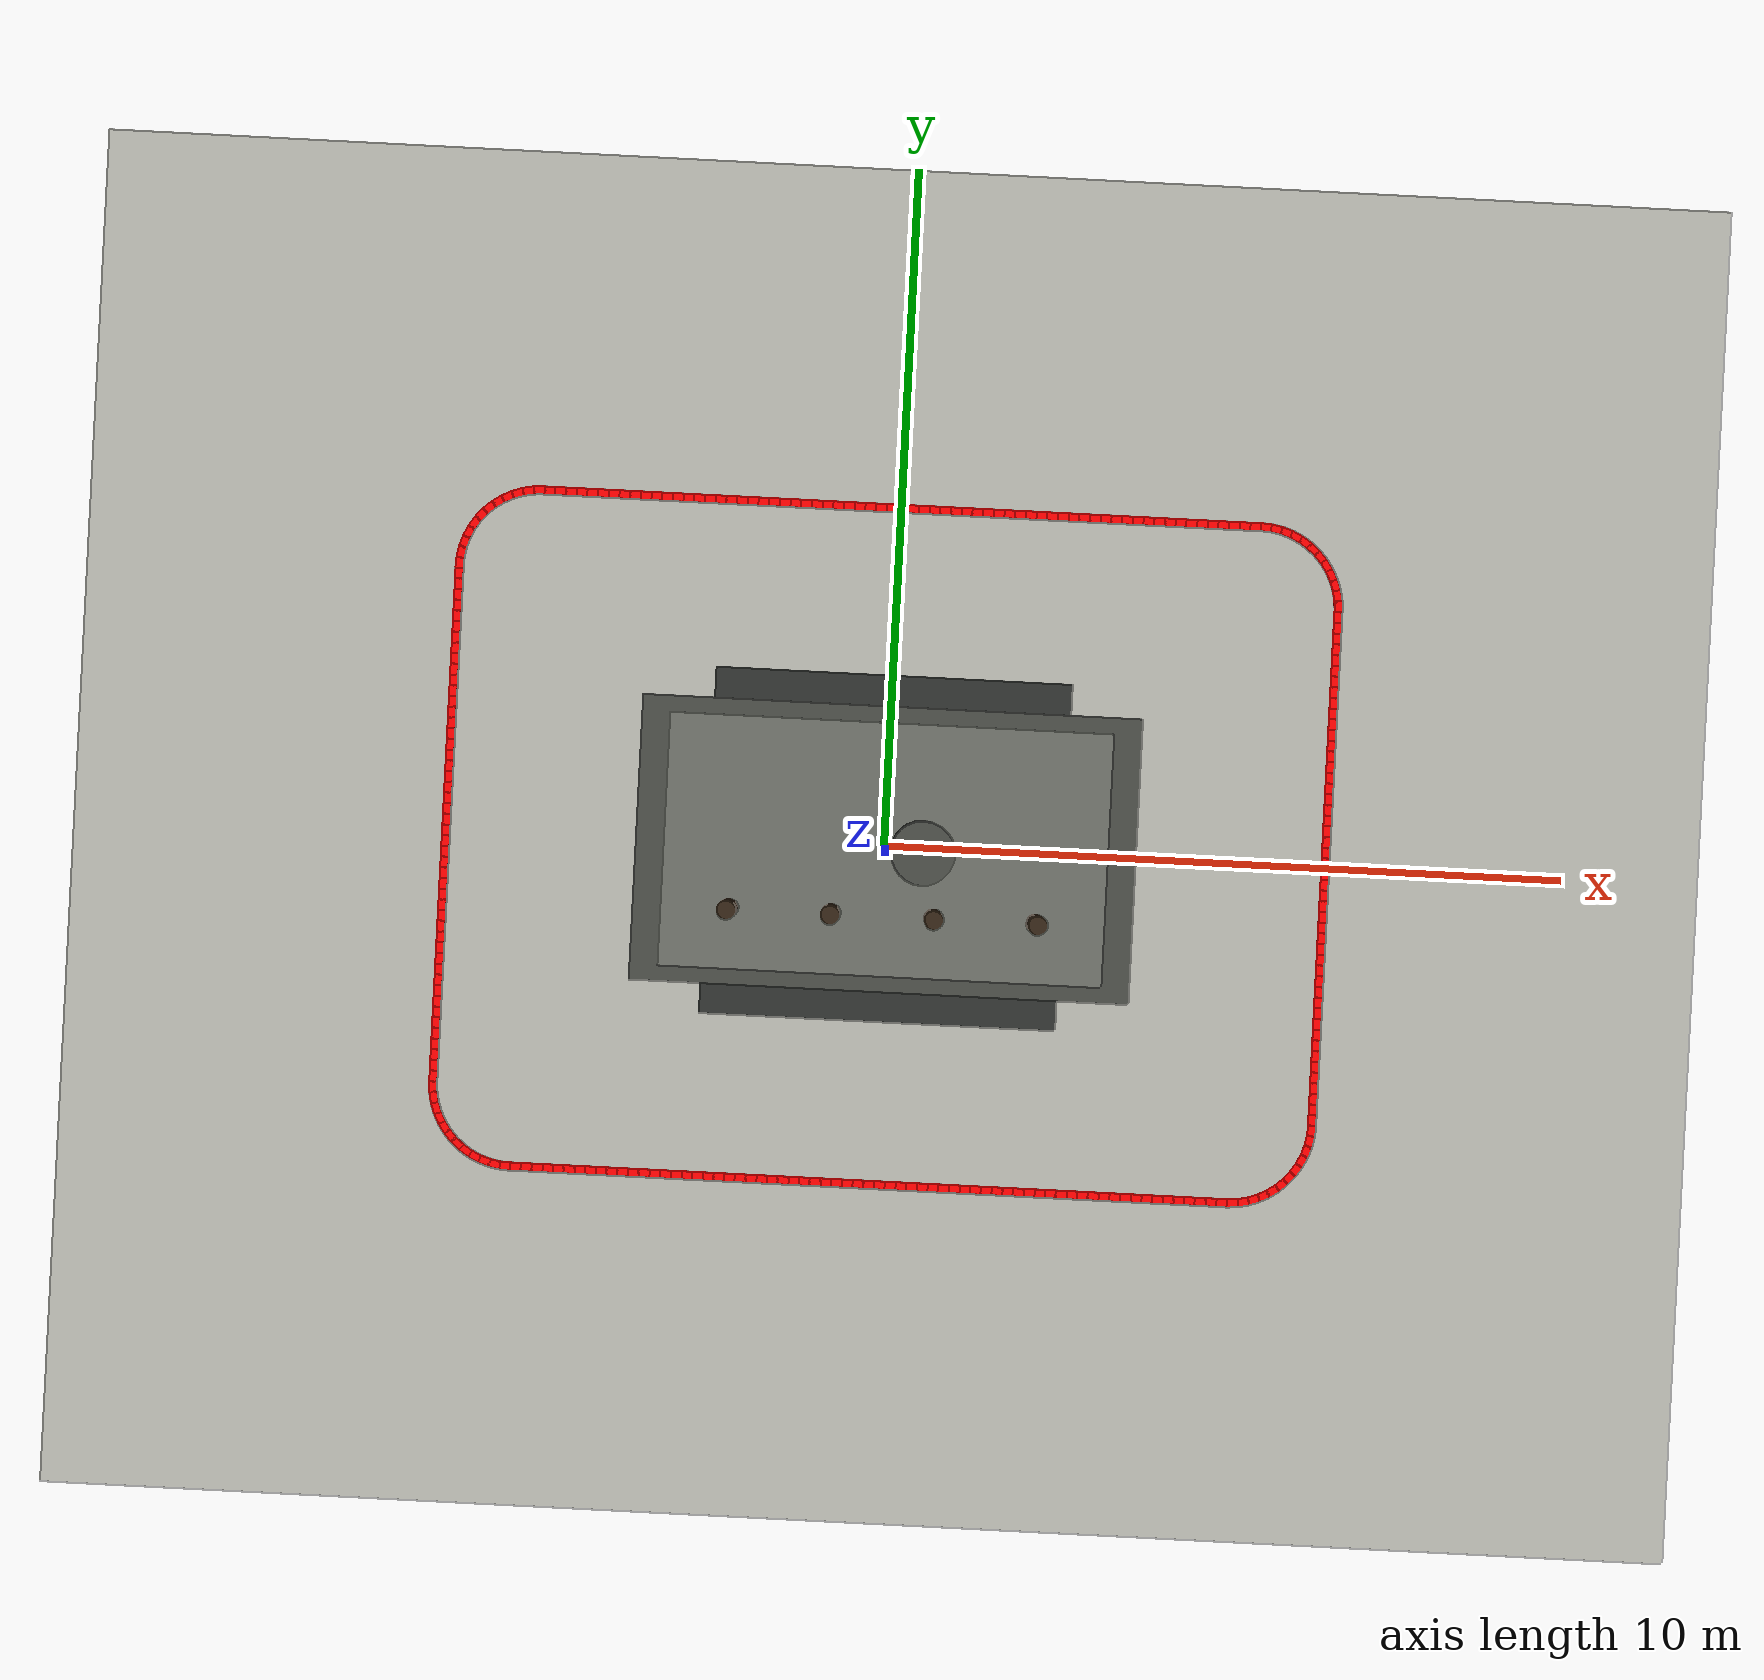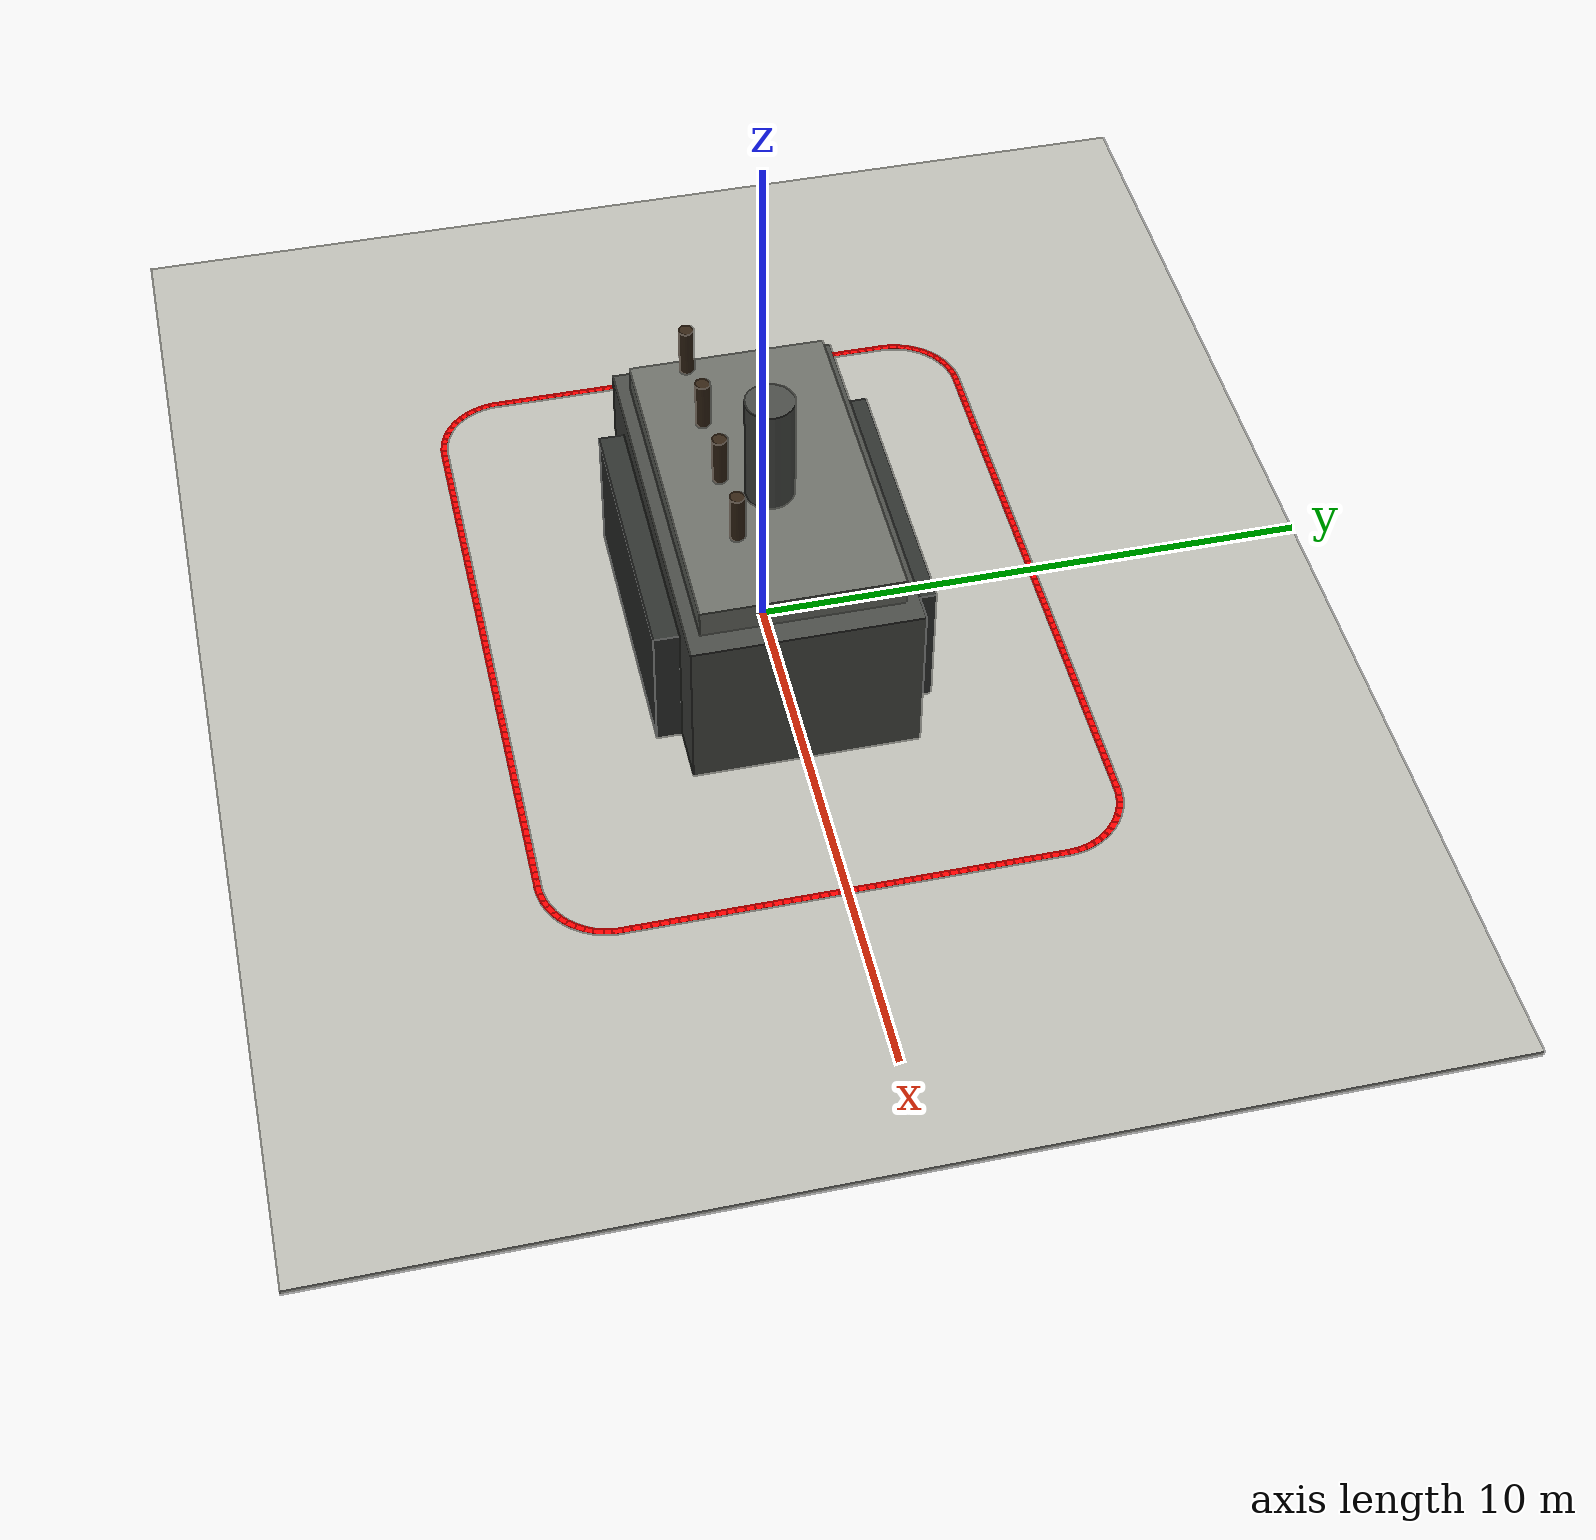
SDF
<sdf version="1.6">
 <world name="transformer_world">
  <gravity>0 0 -9.81</gravity>
  <physics name="ode_physics" type="ode">
   <max_step_size>0.001</max_step_size>
   <real_time_factor>1.0</real_time_factor>
   <real_time_update_rate>1000</real_time_update_rate>
  </physics>
  <scene>
   <ambient>0.70 0.70 0.70 1</ambient>
   <background>0.85 0.85 0.85 1</background>
   <shadows>true</shadows>
  </scene>
  <light name="sun" type="directional">
   <pose>0 0 12 0 0 0</pose>
   <diffuse>0.95 0.95 0.95 1</diffuse>
   <specular>0.20 0.20 0.20 1</specular>
   <direction>-0.3 0.2 -1</direction>
  </light>
  <model name="factory_floor">
   <static>true</static>
   <link name="link">
    <collision name="collision">
     <pose>0 0 -0.05 0 0 0</pose>
     <geometry><box><size>24.0 20.0 0.10</size></box></geometry>
    </collision>
    <visual name="visual">
     <pose>0 0 -0.05 0 0 0</pose>
     <geometry><box><size>24.0 20.0 0.10</size></box></geometry>
     <material><ambient>0.72 0.72 0.69 1</ambient><diffuse>0.72 0.72 0.69 1</diffuse></material>
    </visual>
   </link>
  </model>
  <model name="transformer_main_body">
   <static>true</static>
   <pose>0.0 0.0 1.512 0 0 0</pose>
   <link name="link">
    <collision name="collision"><geometry><box><size>7.0 4.0 3.024</size></box></geometry></collision>
    <visual name="visual">
     <geometry><box><size>7.0 4.0 3.024</size></box></geometry>
     <material><ambient>0.28 0.29 0.27 1</ambient><diffuse>0.28 0.29 0.27 1</diffuse></material>
    </visual>
   </link>
  </model>
  <model name="transformer_top">
   <static>true</static>
   <pose>0.0 0.0 3.274 0 0 0</pose>
   <link name="link">
    <collision name="collision"><geometry><box><size>6.16 3.52 0.5</size></box></geometry></collision>
    <visual name="visual">
     <geometry><box><size>6.16 3.52 0.5</size></box></geometry>
     <material><ambient>0.42 0.43 0.40 1</ambient><diffuse>0.42 0.43 0.40 1</diffuse></material>
    </visual>
   </link>
  </model>
  <model name="radiator_left">
   <static>true</static>
   <pose>0.0 2.225 1.2398399999999998 0 0 0</pose>
   <link name="link">
    <collision name="collision">
     <geometry><box><size>5.04 0.45 2.4796799999999997</size></box></geometry>
    </collision>
    <visual name="visual">
     <geometry><box><size>5.04 0.45 2.4796799999999997</size></box></geometry>
     <material><ambient>0.18 0.19 0.18 1</ambient><diffuse>0.18 0.19 0.18 1</diffuse></material>
    </visual>
   </link>
  </model>
  <model name="radiator_right">
   <static>true</static>
   <pose>0.0 -2.225 1.2398399999999998 0 0 0</pose>
   <link name="link">
    <collision name="collision">
     <geometry><box><size>5.04 0.45 2.4796799999999997</size></box></geometry>
    </collision>
    <visual name="visual">
     <geometry><box><size>5.04 0.45 2.4796799999999997</size></box></geometry>
     <material><ambient>0.18 0.19 0.18 1</ambient><diffuse>0.18 0.19 0.18 1</diffuse></material>
    </visual>
   </link>
  </model>
  <model name="conservator_tank">
   <static>true</static>
   <pose>0.5 0.0 4.45 0 0 0</pose>
   <link name="link">
    <collision name="collision">
     <geometry><cylinder><radius>0.43</radius><length>2.3</length></cylinder></geometry>
    </collision>
    <visual name="visual">
     <geometry><cylinder><radius>0.43</radius><length>2.3</length></cylinder></geometry>
     <material><ambient>0.28 0.29 0.27 1</ambient><diffuse>0.28 0.29 0.27 1</diffuse></material>
    </visual>
   </link>
  </model>
  <model name="transformer_bushing_0">
   <static>true</static>
   <pose>-2.1 -0.9 4.65 0 0 0</pose>
   <link name="link">
    <collision name="collision">
     <geometry><cylinder><radius>0.13</radius><length>0.9</length></cylinder></geometry>
    </collision>
    <visual name="visual">
     <geometry><cylinder><radius>0.13</radius><length>0.9</length></cylinder></geometry>
     <material><ambient>0.20 0.14 0.08 1</ambient><diffuse>0.20 0.14 0.08 1</diffuse></material>
    </visual>
   </link>
  </model>
  <model name="transformer_bushing_1">
   <static>true</static>
   <pose>-0.7 -0.9 4.65 0 0 0</pose>
   <link name="link">
    <collision name="collision">
     <geometry><cylinder><radius>0.13</radius><length>0.9</length></cylinder></geometry>
    </collision>
    <visual name="visual">
     <geometry><cylinder><radius>0.13</radius><length>0.9</length></cylinder></geometry>
     <material><ambient>0.20 0.14 0.08 1</ambient><diffuse>0.20 0.14 0.08 1</diffuse></material>
    </visual>
   </link>
  </model>
  <model name="transformer_bushing_2">
   <static>true</static>
   <pose>0.7 -0.9 4.65 0 0 0</pose>
   <link name="link">
    <collision name="collision">
     <geometry><cylinder><radius>0.13</radius><length>0.9</length></cylinder></geometry>
    </collision>
    <visual name="visual">
     <geometry><cylinder><radius>0.13</radius><length>0.9</length></cylinder></geometry>
     <material><ambient>0.20 0.14 0.08 1</ambient><diffuse>0.20 0.14 0.08 1</diffuse></material>
    </visual>
   </link>
  </model>
  <model name="transformer_bushing_3">
   <static>true</static>
   <pose>2.1 -0.9 4.65 0 0 0</pose>
   <link name="link">
    <collision name="collision">
     <geometry><cylinder><radius>0.13</radius><length>0.9</length></cylinder></geometry>
    </collision>
    <visual name="visual">
     <geometry><cylinder><radius>0.13</radius><length>0.9</length></cylinder></geometry>
     <material><ambient>0.20 0.14 0.08 1</ambient><diffuse>0.20 0.14 0.08 1</diffuse></material>
    </visual>
   </link>
  </model>
  <model name="path_bottom_0">
   <static>true</static>
   <pose>-5.22090 -5.00000 0.00300 0 0 0.00000</pose>
   <link name="link">
    <visual name="visual">
     <cast_shadows>false</cast_shadows>
     <geometry><box><size>0.16821 0.12000 0.00600</size></box></geometry>
     <material><ambient>1 0 0 1</ambient><diffuse>1 0 0 1</diffuse><emissive>0.35 0 0 1</emissive></material>
    </visual>
   </link>
  </model>
  <model name="path_bottom_1">
   <static>true</static>
   <pose>-5.06269 -5.00000 0.00300 0 0 0.00000</pose>
   <link name="link">
    <visual name="visual">
     <cast_shadows>false</cast_shadows>
     <geometry><box><size>0.16821 0.12000 0.00600</size></box></geometry>
     <material><ambient>1 0 0 1</ambient><diffuse>1 0 0 1</diffuse><emissive>0.35 0 0 1</emissive></material>
    </visual>
   </link>
  </model>
  <model name="path_bottom_2">
   <static>true</static>
   <pose>-4.90448 -5.00000 0.00300 0 0 0.00000</pose>
   <link name="link">
    <visual name="visual">
     <cast_shadows>false</cast_shadows>
     <geometry><box><size>0.16821 0.12000 0.00600</size></box></geometry>
     <material><ambient>1 0 0 1</ambient><diffuse>1 0 0 1</diffuse><emissive>0.35 0 0 1</emissive></material>
    </visual>
   </link>
  </model>
  <model name="path_bottom_3">
   <static>true</static>
   <pose>-4.74627 -5.00000 0.00300 0 0 0.00000</pose>
   <link name="link">
    <visual name="visual">
     <cast_shadows>false</cast_shadows>
     <geometry><box><size>0.16821 0.12000 0.00600</size></box></geometry>
     <material><ambient>1 0 0 1</ambient><diffuse>1 0 0 1</diffuse><emissive>0.35 0 0 1</emissive></material>
    </visual>
   </link>
  </model>
  <model name="path_bottom_4">
   <static>true</static>
   <pose>-4.58806 -5.00000 0.00300 0 0 0.00000</pose>
   <link name="link">
    <visual name="visual">
     <cast_shadows>false</cast_shadows>
     <geometry><box><size>0.16821 0.12000 0.00600</size></box></geometry>
     <material><ambient>1 0 0 1</ambient><diffuse>1 0 0 1</diffuse><emissive>0.35 0 0 1</emissive></material>
    </visual>
   </link>
  </model>
  <model name="path_bottom_5">
   <static>true</static>
   <pose>-4.42985 -5.00000 0.00300 0 0 0.00000</pose>
   <link name="link">
    <visual name="visual">
     <cast_shadows>false</cast_shadows>
     <geometry><box><size>0.16821 0.12000 0.00600</size></box></geometry>
     <material><ambient>1 0 0 1</ambient><diffuse>1 0 0 1</diffuse><emissive>0.35 0 0 1</emissive></material>
    </visual>
   </link>
  </model>
  <model name="path_bottom_6">
   <static>true</static>
   <pose>-4.27164 -5.00000 0.00300 0 0 0.00000</pose>
   <link name="link">
    <visual name="visual">
     <cast_shadows>false</cast_shadows>
     <geometry><box><size>0.16821 0.12000 0.00600</size></box></geometry>
     <material><ambient>1 0 0 1</ambient><diffuse>1 0 0 1</diffuse><emissive>0.35 0 0 1</emissive></material>
    </visual>
   </link>
  </model>
  <model name="path_bottom_7">
   <static>true</static>
   <pose>-4.11343 -5.00000 0.00300 0 0 0.00000</pose>
   <link name="link">
    <visual name="visual">
     <cast_shadows>false</cast_shadows>
     <geometry><box><size>0.16821 0.12000 0.00600</size></box></geometry>
     <material><ambient>1 0 0 1</ambient><diffuse>1 0 0 1</diffuse><emissive>0.35 0 0 1</emissive></material>
    </visual>
   </link>
  </model>
  <model name="path_bottom_8">
   <static>true</static>
   <pose>-3.95522 -5.00000 0.00300 0 0 0.00000</pose>
   <link name="link">
    <visual name="visual">
     <cast_shadows>false</cast_shadows>
     <geometry><box><size>0.16821 0.12000 0.00600</size></box></geometry>
     <material><ambient>1 0 0 1</ambient><diffuse>1 0 0 1</diffuse><emissive>0.35 0 0 1</emissive></material>
    </visual>
   </link>
  </model>
  <model name="path_bottom_9">
   <static>true</static>
   <pose>-3.79701 -5.00000 0.00300 0 0 0.00000</pose>
   <link name="link">
    <visual name="visual">
     <cast_shadows>false</cast_shadows>
     <geometry><box><size>0.16821 0.12000 0.00600</size></box></geometry>
     <material><ambient>1 0 0 1</ambient><diffuse>1 0 0 1</diffuse><emissive>0.35 0 0 1</emissive></material>
    </visual>
   </link>
  </model>
  <model name="path_bottom_10">
   <static>true</static>
   <pose>-3.63881 -5.00000 0.00300 0 0 0.00000</pose>
   <link name="link">
    <visual name="visual">
     <cast_shadows>false</cast_shadows>
     <geometry><box><size>0.16821 0.12000 0.00600</size></box></geometry>
     <material><ambient>1 0 0 1</ambient><diffuse>1 0 0 1</diffuse><emissive>0.35 0 0 1</emissive></material>
    </visual>
   </link>
  </model>
  <model name="path_bottom_11">
   <static>true</static>
   <pose>-3.48060 -5.00000 0.00300 0 0 0.00000</pose>
   <link name="link">
    <visual name="visual">
     <cast_shadows>false</cast_shadows>
     <geometry><box><size>0.16821 0.12000 0.00600</size></box></geometry>
     <material><ambient>1 0 0 1</ambient><diffuse>1 0 0 1</diffuse><emissive>0.35 0 0 1</emissive></material>
    </visual>
   </link>
  </model>
  <model name="path_bottom_12">
   <static>true</static>
   <pose>-3.32239 -5.00000 0.00300 0 0 0.00000</pose>
   <link name="link">
    <visual name="visual">
     <cast_shadows>false</cast_shadows>
     <geometry><box><size>0.16821 0.12000 0.00600</size></box></geometry>
     <material><ambient>1 0 0 1</ambient><diffuse>1 0 0 1</diffuse><emissive>0.35 0 0 1</emissive></material>
    </visual>
   </link>
  </model>
  <model name="path_bottom_13">
   <static>true</static>
   <pose>-3.16418 -5.00000 0.00300 0 0 0.00000</pose>
   <link name="link">
    <visual name="visual">
     <cast_shadows>false</cast_shadows>
     <geometry><box><size>0.16821 0.12000 0.00600</size></box></geometry>
     <material><ambient>1 0 0 1</ambient><diffuse>1 0 0 1</diffuse><emissive>0.35 0 0 1</emissive></material>
    </visual>
   </link>
  </model>
  <model name="path_bottom_14">
   <static>true</static>
   <pose>-3.00597 -5.00000 0.00300 0 0 0.00000</pose>
   <link name="link">
    <visual name="visual">
     <cast_shadows>false</cast_shadows>
     <geometry><box><size>0.16821 0.12000 0.00600</size></box></geometry>
     <material><ambient>1 0 0 1</ambient><diffuse>1 0 0 1</diffuse><emissive>0.35 0 0 1</emissive></material>
    </visual>
   </link>
  </model>
  <model name="path_bottom_15">
   <static>true</static>
   <pose>-2.84776 -5.00000 0.00300 0 0 0.00000</pose>
   <link name="link">
    <visual name="visual">
     <cast_shadows>false</cast_shadows>
     <geometry><box><size>0.16821 0.12000 0.00600</size></box></geometry>
     <material><ambient>1 0 0 1</ambient><diffuse>1 0 0 1</diffuse><emissive>0.35 0 0 1</emissive></material>
    </visual>
   </link>
  </model>
  <model name="path_bottom_16">
   <static>true</static>
   <pose>-2.68955 -5.00000 0.00300 0 0 0.00000</pose>
   <link name="link">
    <visual name="visual">
     <cast_shadows>false</cast_shadows>
     <geometry><box><size>0.16821 0.12000 0.00600</size></box></geometry>
     <material><ambient>1 0 0 1</ambient><diffuse>1 0 0 1</diffuse><emissive>0.35 0 0 1</emissive></material>
    </visual>
   </link>
  </model>
  <model name="path_bottom_17">
   <static>true</static>
   <pose>-2.53134 -5.00000 0.00300 0 0 0.00000</pose>
   <link name="link">
    <visual name="visual">
     <cast_shadows>false</cast_shadows>
     <geometry><box><size>0.16821 0.12000 0.00600</size></box></geometry>
     <material><ambient>1 0 0 1</ambient><diffuse>1 0 0 1</diffuse><emissive>0.35 0 0 1</emissive></material>
    </visual>
   </link>
  </model>
  <model name="path_bottom_18">
   <static>true</static>
   <pose>-2.37313 -5.00000 0.00300 0 0 0.00000</pose>
   <link name="link">
    <visual name="visual">
     <cast_shadows>false</cast_shadows>
     <geometry><box><size>0.16821 0.12000 0.00600</size></box></geometry>
     <material><ambient>1 0 0 1</ambient><diffuse>1 0 0 1</diffuse><emissive>0.35 0 0 1</emissive></material>
    </visual>
   </link>
  </model>
  <model name="path_bottom_19">
   <static>true</static>
   <pose>-2.21493 -5.00000 0.00300 0 0 0.00000</pose>
   <link name="link">
    <visual name="visual">
     <cast_shadows>false</cast_shadows>
     <geometry><box><size>0.16821 0.12000 0.00600</size></box></geometry>
     <material><ambient>1 0 0 1</ambient><diffuse>1 0 0 1</diffuse><emissive>0.35 0 0 1</emissive></material>
    </visual>
   </link>
  </model>
  <model name="path_bottom_20">
   <static>true</static>
   <pose>-2.05672 -5.00000 0.00300 0 0 0.00000</pose>
   <link name="link">
    <visual name="visual">
     <cast_shadows>false</cast_shadows>
     <geometry><box><size>0.16821 0.12000 0.00600</size></box></geometry>
     <material><ambient>1 0 0 1</ambient><diffuse>1 0 0 1</diffuse><emissive>0.35 0 0 1</emissive></material>
    </visual>
   </link>
  </model>
  <model name="path_bottom_21">
   <static>true</static>
   <pose>-1.89851 -5.00000 0.00300 0 0 0.00000</pose>
   <link name="link">
    <visual name="visual">
     <cast_shadows>false</cast_shadows>
     <geometry><box><size>0.16821 0.12000 0.00600</size></box></geometry>
     <material><ambient>1 0 0 1</ambient><diffuse>1 0 0 1</diffuse><emissive>0.35 0 0 1</emissive></material>
    </visual>
   </link>
  </model>
  <model name="path_bottom_22">
   <static>true</static>
   <pose>-1.74030 -5.00000 0.00300 0 0 0.00000</pose>
   <link name="link">
    <visual name="visual">
     <cast_shadows>false</cast_shadows>
     <geometry><box><size>0.16821 0.12000 0.00600</size></box></geometry>
     <material><ambient>1 0 0 1</ambient><diffuse>1 0 0 1</diffuse><emissive>0.35 0 0 1</emissive></material>
    </visual>
   </link>
  </model>
  <model name="path_bottom_23">
   <static>true</static>
   <pose>-1.58209 -5.00000 0.00300 0 0 0.00000</pose>
   <link name="link">
    <visual name="visual">
     <cast_shadows>false</cast_shadows>
     <geometry><box><size>0.16821 0.12000 0.00600</size></box></geometry>
     <material><ambient>1 0 0 1</ambient><diffuse>1 0 0 1</diffuse><emissive>0.35 0 0 1</emissive></material>
    </visual>
   </link>
  </model>
  <model name="path_bottom_24">
   <static>true</static>
   <pose>-1.42388 -5.00000 0.00300 0 0 0.00000</pose>
   <link name="link">
    <visual name="visual">
     <cast_shadows>false</cast_shadows>
     <geometry><box><size>0.16821 0.12000 0.00600</size></box></geometry>
     <material><ambient>1 0 0 1</ambient><diffuse>1 0 0 1</diffuse><emissive>0.35 0 0 1</emissive></material>
    </visual>
   </link>
  </model>
  <model name="path_bottom_25">
   <static>true</static>
   <pose>-1.26567 -5.00000 0.00300 0 0 0.00000</pose>
   <link name="link">
    <visual name="visual">
     <cast_shadows>false</cast_shadows>
     <geometry><box><size>0.16821 0.12000 0.00600</size></box></geometry>
     <material><ambient>1 0 0 1</ambient><diffuse>1 0 0 1</diffuse><emissive>0.35 0 0 1</emissive></material>
    </visual>
   </link>
  </model>
  <model name="path_bottom_26">
   <static>true</static>
   <pose>-1.10746 -5.00000 0.00300 0 0 0.00000</pose>
   <link name="link">
    <visual name="visual">
     <cast_shadows>false</cast_shadows>
     <geometry><box><size>0.16821 0.12000 0.00600</size></box></geometry>
     <material><ambient>1 0 0 1</ambient><diffuse>1 0 0 1</diffuse><emissive>0.35 0 0 1</emissive></material>
    </visual>
   </link>
  </model>
  <model name="path_bottom_27">
   <static>true</static>
   <pose>-0.94925 -5.00000 0.00300 0 0 0.00000</pose>
   <link name="link">
    <visual name="visual">
     <cast_shadows>false</cast_shadows>
     <geometry><box><size>0.16821 0.12000 0.00600</size></box></geometry>
     <material><ambient>1 0 0 1</ambient><diffuse>1 0 0 1</diffuse><emissive>0.35 0 0 1</emissive></material>
    </visual>
   </link>
  </model>
  <model name="path_bottom_28">
   <static>true</static>
   <pose>-0.79104 -5.00000 0.00300 0 0 0.00000</pose>
   <link name="link">
    <visual name="visual">
     <cast_shadows>false</cast_shadows>
     <geometry><box><size>0.16821 0.12000 0.00600</size></box></geometry>
     <material><ambient>1 0 0 1</ambient><diffuse>1 0 0 1</diffuse><emissive>0.35 0 0 1</emissive></material>
    </visual>
   </link>
  </model>
  <model name="path_bottom_29">
   <static>true</static>
   <pose>-0.63284 -5.00000 0.00300 0 0 0.00000</pose>
   <link name="link">
    <visual name="visual">
     <cast_shadows>false</cast_shadows>
     <geometry><box><size>0.16821 0.12000 0.00600</size></box></geometry>
     <material><ambient>1 0 0 1</ambient><diffuse>1 0 0 1</diffuse><emissive>0.35 0 0 1</emissive></material>
    </visual>
   </link>
  </model>
  <model name="path_bottom_30">
   <static>true</static>
   <pose>-0.47463 -5.00000 0.00300 0 0 0.00000</pose>
   <link name="link">
    <visual name="visual">
     <cast_shadows>false</cast_shadows>
     <geometry><box><size>0.16821 0.12000 0.00600</size></box></geometry>
     <material><ambient>1 0 0 1</ambient><diffuse>1 0 0 1</diffuse><emissive>0.35 0 0 1</emissive></material>
    </visual>
   </link>
  </model>
  <model name="path_bottom_31">
   <static>true</static>
   <pose>-0.31642 -5.00000 0.00300 0 0 0.00000</pose>
   <link name="link">
    <visual name="visual">
     <cast_shadows>false</cast_shadows>
     <geometry><box><size>0.16821 0.12000 0.00600</size></box></geometry>
     <material><ambient>1 0 0 1</ambient><diffuse>1 0 0 1</diffuse><emissive>0.35 0 0 1</emissive></material>
    </visual>
   </link>
  </model>
  <model name="path_bottom_32">
   <static>true</static>
   <pose>-0.15821 -5.00000 0.00300 0 0 0.00000</pose>
   <link name="link">
    <visual name="visual">
     <cast_shadows>false</cast_shadows>
     <geometry><box><size>0.16821 0.12000 0.00600</size></box></geometry>
     <material><ambient>1 0 0 1</ambient><diffuse>1 0 0 1</diffuse><emissive>0.35 0 0 1</emissive></material>
    </visual>
   </link>
  </model>
  <model name="path_bottom_33">
   <static>true</static>
   <pose>0.00000 -5.00000 0.00300 0 0 0.00000</pose>
   <link name="link">
    <visual name="visual">
     <cast_shadows>false</cast_shadows>
     <geometry><box><size>0.16821 0.12000 0.00600</size></box></geometry>
     <material><ambient>1 0 0 1</ambient><diffuse>1 0 0 1</diffuse><emissive>0.35 0 0 1</emissive></material>
    </visual>
   </link>
  </model>
  <model name="path_bottom_34">
   <static>true</static>
   <pose>0.15821 -5.00000 0.00300 0 0 0.00000</pose>
   <link name="link">
    <visual name="visual">
     <cast_shadows>false</cast_shadows>
     <geometry><box><size>0.16821 0.12000 0.00600</size></box></geometry>
     <material><ambient>1 0 0 1</ambient><diffuse>1 0 0 1</diffuse><emissive>0.35 0 0 1</emissive></material>
    </visual>
   </link>
  </model>
  <model name="path_bottom_35">
   <static>true</static>
   <pose>0.31642 -5.00000 0.00300 0 0 0.00000</pose>
   <link name="link">
    <visual name="visual">
     <cast_shadows>false</cast_shadows>
     <geometry><box><size>0.16821 0.12000 0.00600</size></box></geometry>
     <material><ambient>1 0 0 1</ambient><diffuse>1 0 0 1</diffuse><emissive>0.35 0 0 1</emissive></material>
    </visual>
   </link>
  </model>
  <model name="path_bottom_36">
   <static>true</static>
   <pose>0.47463 -5.00000 0.00300 0 0 0.00000</pose>
   <link name="link">
    <visual name="visual">
     <cast_shadows>false</cast_shadows>
     <geometry><box><size>0.16821 0.12000 0.00600</size></box></geometry>
     <material><ambient>1 0 0 1</ambient><diffuse>1 0 0 1</diffuse><emissive>0.35 0 0 1</emissive></material>
    </visual>
   </link>
  </model>
  <model name="path_bottom_37">
   <static>true</static>
   <pose>0.63284 -5.00000 0.00300 0 0 0.00000</pose>
   <link name="link">
    <visual name="visual">
     <cast_shadows>false</cast_shadows>
     <geometry><box><size>0.16821 0.12000 0.00600</size></box></geometry>
     <material><ambient>1 0 0 1</ambient><diffuse>1 0 0 1</diffuse><emissive>0.35 0 0 1</emissive></material>
    </visual>
   </link>
  </model>
  <model name="path_bottom_38">
   <static>true</static>
   <pose>0.79104 -5.00000 0.00300 0 0 0.00000</pose>
   <link name="link">
    <visual name="visual">
     <cast_shadows>false</cast_shadows>
     <geometry><box><size>0.16821 0.12000 0.00600</size></box></geometry>
     <material><ambient>1 0 0 1</ambient><diffuse>1 0 0 1</diffuse><emissive>0.35 0 0 1</emissive></material>
    </visual>
   </link>
  </model>
  <model name="path_bottom_39">
   <static>true</static>
   <pose>0.94925 -5.00000 0.00300 0 0 0.00000</pose>
   <link name="link">
    <visual name="visual">
     <cast_shadows>false</cast_shadows>
     <geometry><box><size>0.16821 0.12000 0.00600</size></box></geometry>
     <material><ambient>1 0 0 1</ambient><diffuse>1 0 0 1</diffuse><emissive>0.35 0 0 1</emissive></material>
    </visual>
   </link>
  </model>
  <model name="path_bottom_40">
   <static>true</static>
   <pose>1.10746 -5.00000 0.00300 0 0 0.00000</pose>
   <link name="link">
    <visual name="visual">
     <cast_shadows>false</cast_shadows>
     <geometry><box><size>0.16821 0.12000 0.00600</size></box></geometry>
     <material><ambient>1 0 0 1</ambient><diffuse>1 0 0 1</diffuse><emissive>0.35 0 0 1</emissive></material>
    </visual>
   </link>
  </model>
  <model name="path_bottom_41">
   <static>true</static>
   <pose>1.26567 -5.00000 0.00300 0 0 0.00000</pose>
   <link name="link">
    <visual name="visual">
     <cast_shadows>false</cast_shadows>
     <geometry><box><size>0.16821 0.12000 0.00600</size></box></geometry>
     <material><ambient>1 0 0 1</ambient><diffuse>1 0 0 1</diffuse><emissive>0.35 0 0 1</emissive></material>
    </visual>
   </link>
  </model>
  <model name="path_bottom_42">
   <static>true</static>
   <pose>1.42388 -5.00000 0.00300 0 0 0.00000</pose>
   <link name="link">
    <visual name="visual">
     <cast_shadows>false</cast_shadows>
     <geometry><box><size>0.16821 0.12000 0.00600</size></box></geometry>
     <material><ambient>1 0 0 1</ambient><diffuse>1 0 0 1</diffuse><emissive>0.35 0 0 1</emissive></material>
    </visual>
   </link>
  </model>
  <model name="path_bottom_43">
   <static>true</static>
   <pose>1.58209 -5.00000 0.00300 0 0 0.00000</pose>
   <link name="link">
    <visual name="visual">
     <cast_shadows>false</cast_shadows>
     <geometry><box><size>0.16821 0.12000 0.00600</size></box></geometry>
     <material><ambient>1 0 0 1</ambient><diffuse>1 0 0 1</diffuse><emissive>0.35 0 0 1</emissive></material>
    </visual>
   </link>
  </model>
  <model name="path_bottom_44">
   <static>true</static>
   <pose>1.74030 -5.00000 0.00300 0 0 0.00000</pose>
   <link name="link">
    <visual name="visual">
     <cast_shadows>false</cast_shadows>
     <geometry><box><size>0.16821 0.12000 0.00600</size></box></geometry>
     <material><ambient>1 0 0 1</ambient><diffuse>1 0 0 1</diffuse><emissive>0.35 0 0 1</emissive></material>
    </visual>
   </link>
  </model>
  <model name="path_bottom_45">
   <static>true</static>
   <pose>1.89851 -5.00000 0.00300 0 0 0.00000</pose>
   <link name="link">
    <visual name="visual">
     <cast_shadows>false</cast_shadows>
     <geometry><box><size>0.16821 0.12000 0.00600</size></box></geometry>
     <material><ambient>1 0 0 1</ambient><diffuse>1 0 0 1</diffuse><emissive>0.35 0 0 1</emissive></material>
    </visual>
   </link>
  </model>
  <model name="path_bottom_46">
   <static>true</static>
   <pose>2.05672 -5.00000 0.00300 0 0 0.00000</pose>
   <link name="link">
    <visual name="visual">
     <cast_shadows>false</cast_shadows>
     <geometry><box><size>0.16821 0.12000 0.00600</size></box></geometry>
     <material><ambient>1 0 0 1</ambient><diffuse>1 0 0 1</diffuse><emissive>0.35 0 0 1</emissive></material>
    </visual>
   </link>
  </model>
  <model name="path_bottom_47">
   <static>true</static>
   <pose>2.21493 -5.00000 0.00300 0 0 0.00000</pose>
   <link name="link">
    <visual name="visual">
     <cast_shadows>false</cast_shadows>
     <geometry><box><size>0.16821 0.12000 0.00600</size></box></geometry>
     <material><ambient>1 0 0 1</ambient><diffuse>1 0 0 1</diffuse><emissive>0.35 0 0 1</emissive></material>
    </visual>
   </link>
  </model>
  <model name="path_bottom_48">
   <static>true</static>
   <pose>2.37313 -5.00000 0.00300 0 0 0.00000</pose>
   <link name="link">
    <visual name="visual">
     <cast_shadows>false</cast_shadows>
     <geometry><box><size>0.16821 0.12000 0.00600</size></box></geometry>
     <material><ambient>1 0 0 1</ambient><diffuse>1 0 0 1</diffuse><emissive>0.35 0 0 1</emissive></material>
    </visual>
   </link>
  </model>
  <model name="path_bottom_49">
   <static>true</static>
   <pose>2.53134 -5.00000 0.00300 0 0 0.00000</pose>
   <link name="link">
    <visual name="visual">
     <cast_shadows>false</cast_shadows>
     <geometry><box><size>0.16821 0.12000 0.00600</size></box></geometry>
     <material><ambient>1 0 0 1</ambient><diffuse>1 0 0 1</diffuse><emissive>0.35 0 0 1</emissive></material>
    </visual>
   </link>
  </model>
  <model name="path_bottom_50">
   <static>true</static>
   <pose>2.68955 -5.00000 0.00300 0 0 0.00000</pose>
   <link name="link">
    <visual name="visual">
     <cast_shadows>false</cast_shadows>
     <geometry><box><size>0.16821 0.12000 0.00600</size></box></geometry>
     <material><ambient>1 0 0 1</ambient><diffuse>1 0 0 1</diffuse><emissive>0.35 0 0 1</emissive></material>
    </visual>
   </link>
  </model>
  <model name="path_bottom_51">
   <static>true</static>
   <pose>2.84776 -5.00000 0.00300 0 0 0.00000</pose>
   <link name="link">
    <visual name="visual">
     <cast_shadows>false</cast_shadows>
     <geometry><box><size>0.16821 0.12000 0.00600</size></box></geometry>
     <material><ambient>1 0 0 1</ambient><diffuse>1 0 0 1</diffuse><emissive>0.35 0 0 1</emissive></material>
    </visual>
   </link>
  </model>
  <model name="path_bottom_52">
   <static>true</static>
   <pose>3.00597 -5.00000 0.00300 0 0 0.00000</pose>
   <link name="link">
    <visual name="visual">
     <cast_shadows>false</cast_shadows>
     <geometry><box><size>0.16821 0.12000 0.00600</size></box></geometry>
     <material><ambient>1 0 0 1</ambient><diffuse>1 0 0 1</diffuse><emissive>0.35 0 0 1</emissive></material>
    </visual>
   </link>
  </model>
  <model name="path_bottom_53">
   <static>true</static>
   <pose>3.16418 -5.00000 0.00300 0 0 0.00000</pose>
   <link name="link">
    <visual name="visual">
     <cast_shadows>false</cast_shadows>
     <geometry><box><size>0.16821 0.12000 0.00600</size></box></geometry>
     <material><ambient>1 0 0 1</ambient><diffuse>1 0 0 1</diffuse><emissive>0.35 0 0 1</emissive></material>
    </visual>
   </link>
  </model>
  <model name="path_bottom_54">
   <static>true</static>
   <pose>3.32239 -5.00000 0.00300 0 0 0.00000</pose>
   <link name="link">
    <visual name="visual">
     <cast_shadows>false</cast_shadows>
     <geometry><box><size>0.16821 0.12000 0.00600</size></box></geometry>
     <material><ambient>1 0 0 1</ambient><diffuse>1 0 0 1</diffuse><emissive>0.35 0 0 1</emissive></material>
    </visual>
   </link>
  </model>
  <model name="path_bottom_55">
   <static>true</static>
   <pose>3.48060 -5.00000 0.00300 0 0 0.00000</pose>
   <link name="link">
    <visual name="visual">
     <cast_shadows>false</cast_shadows>
     <geometry><box><size>0.16821 0.12000 0.00600</size></box></geometry>
     <material><ambient>1 0 0 1</ambient><diffuse>1 0 0 1</diffuse><emissive>0.35 0 0 1</emissive></material>
    </visual>
   </link>
  </model>
  <model name="path_bottom_56">
   <static>true</static>
   <pose>3.63881 -5.00000 0.00300 0 0 0.00000</pose>
   <link name="link">
    <visual name="visual">
     <cast_shadows>false</cast_shadows>
     <geometry><box><size>0.16821 0.12000 0.00600</size></box></geometry>
     <material><ambient>1 0 0 1</ambient><diffuse>1 0 0 1</diffuse><emissive>0.35 0 0 1</emissive></material>
    </visual>
   </link>
  </model>
  <model name="path_bottom_57">
   <static>true</static>
   <pose>3.79701 -5.00000 0.00300 0 0 0.00000</pose>
   <link name="link">
    <visual name="visual">
     <cast_shadows>false</cast_shadows>
     <geometry><box><size>0.16821 0.12000 0.00600</size></box></geometry>
     <material><ambient>1 0 0 1</ambient><diffuse>1 0 0 1</diffuse><emissive>0.35 0 0 1</emissive></material>
    </visual>
   </link>
  </model>
  <model name="path_bottom_58">
   <static>true</static>
   <pose>3.95522 -5.00000 0.00300 0 0 0.00000</pose>
   <link name="link">
    <visual name="visual">
     <cast_shadows>false</cast_shadows>
     <geometry><box><size>0.16821 0.12000 0.00600</size></box></geometry>
     <material><ambient>1 0 0 1</ambient><diffuse>1 0 0 1</diffuse><emissive>0.35 0 0 1</emissive></material>
    </visual>
   </link>
  </model>
  <model name="path_bottom_59">
   <static>true</static>
   <pose>4.11343 -5.00000 0.00300 0 0 0.00000</pose>
   <link name="link">
    <visual name="visual">
     <cast_shadows>false</cast_shadows>
     <geometry><box><size>0.16821 0.12000 0.00600</size></box></geometry>
     <material><ambient>1 0 0 1</ambient><diffuse>1 0 0 1</diffuse><emissive>0.35 0 0 1</emissive></material>
    </visual>
   </link>
  </model>
  <model name="path_bottom_60">
   <static>true</static>
   <pose>4.27164 -5.00000 0.00300 0 0 0.00000</pose>
   <link name="link">
    <visual name="visual">
     <cast_shadows>false</cast_shadows>
     <geometry><box><size>0.16821 0.12000 0.00600</size></box></geometry>
     <material><ambient>1 0 0 1</ambient><diffuse>1 0 0 1</diffuse><emissive>0.35 0 0 1</emissive></material>
    </visual>
   </link>
  </model>
  <model name="path_bottom_61">
   <static>true</static>
   <pose>4.42985 -5.00000 0.00300 0 0 0.00000</pose>
   <link name="link">
    <visual name="visual">
     <cast_shadows>false</cast_shadows>
     <geometry><box><size>0.16821 0.12000 0.00600</size></box></geometry>
     <material><ambient>1 0 0 1</ambient><diffuse>1 0 0 1</diffuse><emissive>0.35 0 0 1</emissive></material>
    </visual>
   </link>
  </model>
  <model name="path_bottom_62">
   <static>true</static>
   <pose>4.58806 -5.00000 0.00300 0 0 0.00000</pose>
   <link name="link">
    <visual name="visual">
     <cast_shadows>false</cast_shadows>
     <geometry><box><size>0.16821 0.12000 0.00600</size></box></geometry>
     <material><ambient>1 0 0 1</ambient><diffuse>1 0 0 1</diffuse><emissive>0.35 0 0 1</emissive></material>
    </visual>
   </link>
  </model>
  <model name="path_bottom_63">
   <static>true</static>
   <pose>4.74627 -5.00000 0.00300 0 0 0.00000</pose>
   <link name="link">
    <visual name="visual">
     <cast_shadows>false</cast_shadows>
     <geometry><box><size>0.16821 0.12000 0.00600</size></box></geometry>
     <material><ambient>1 0 0 1</ambient><diffuse>1 0 0 1</diffuse><emissive>0.35 0 0 1</emissive></material>
    </visual>
   </link>
  </model>
  <model name="path_bottom_64">
   <static>true</static>
   <pose>4.90448 -5.00000 0.00300 0 0 0.00000</pose>
   <link name="link">
    <visual name="visual">
     <cast_shadows>false</cast_shadows>
     <geometry><box><size>0.16821 0.12000 0.00600</size></box></geometry>
     <material><ambient>1 0 0 1</ambient><diffuse>1 0 0 1</diffuse><emissive>0.35 0 0 1</emissive></material>
    </visual>
   </link>
  </model>
  <model name="path_bottom_65">
   <static>true</static>
   <pose>5.06269 -5.00000 0.00300 0 0 0.00000</pose>
   <link name="link">
    <visual name="visual">
     <cast_shadows>false</cast_shadows>
     <geometry><box><size>0.16821 0.12000 0.00600</size></box></geometry>
     <material><ambient>1 0 0 1</ambient><diffuse>1 0 0 1</diffuse><emissive>0.35 0 0 1</emissive></material>
    </visual>
   </link>
  </model>
  <model name="path_bottom_66">
   <static>true</static>
   <pose>5.22090 -5.00000 0.00300 0 0 0.00000</pose>
   <link name="link">
    <visual name="visual">
     <cast_shadows>false</cast_shadows>
     <geometry><box><size>0.16821 0.12000 0.00600</size></box></geometry>
     <material><ambient>1 0 0 1</ambient><diffuse>1 0 0 1</diffuse><emissive>0.35 0 0 1</emissive></material>
    </visual>
   </link>
  </model>
  <model name="path_corner_br_0">
   <static>true</static>
   <pose>5.37848 -4.99743 0.00300 0 0 0.06545</pose>
   <link name="link">
    <visual name="visual">
     <cast_shadows>false</cast_shadows>
     <geometry><box><size>0.17708 0.12000 0.00600</size></box></geometry>
     <material><ambient>1 0 0 1</ambient><diffuse>1 0 0 1</diffuse><emissive>0.35 0 0 1</emissive></material>
    </visual>
   </link>
  </model>
  <model name="path_corner_br_1">
   <static>true</static>
   <pose>5.53411 -4.97694 0.00300 0 0 0.19635</pose>
   <link name="link">
    <visual name="visual">
     <cast_shadows>false</cast_shadows>
     <geometry><box><size>0.17708 0.12000 0.00600</size></box></geometry>
     <material><ambient>1 0 0 1</ambient><diffuse>1 0 0 1</diffuse><emissive>0.35 0 0 1</emissive></material>
    </visual>
   </link>
  </model>
  <model name="path_corner_br_2">
   <static>true</static>
   <pose>5.68573 -4.93632 0.00300 0 0 0.32725</pose>
   <link name="link">
    <visual name="visual">
     <cast_shadows>false</cast_shadows>
     <geometry><box><size>0.17708 0.12000 0.00600</size></box></geometry>
     <material><ambient>1 0 0 1</ambient><diffuse>1 0 0 1</diffuse><emissive>0.35 0 0 1</emissive></material>
    </visual>
   </link>
  </model>
  <model name="path_corner_br_3">
   <static>true</static>
   <pose>5.83075 -4.87625 0.00300 0 0 0.45815</pose>
   <link name="link">
    <visual name="visual">
     <cast_shadows>false</cast_shadows>
     <geometry><box><size>0.17708 0.12000 0.00600</size></box></geometry>
     <material><ambient>1 0 0 1</ambient><diffuse>1 0 0 1</diffuse><emissive>0.35 0 0 1</emissive></material>
    </visual>
   </link>
  </model>
  <model name="path_corner_br_4">
   <static>true</static>
   <pose>5.96668 -4.79776 0.00300 0 0 0.58905</pose>
   <link name="link">
    <visual name="visual">
     <cast_shadows>false</cast_shadows>
     <geometry><box><size>0.17708 0.12000 0.00600</size></box></geometry>
     <material><ambient>1 0 0 1</ambient><diffuse>1 0 0 1</diffuse><emissive>0.35 0 0 1</emissive></material>
    </visual>
   </link>
  </model>
  <model name="path_corner_br_5">
   <static>true</static>
   <pose>6.09121 -4.70221 0.00300 0 0 0.71995</pose>
   <link name="link">
    <visual name="visual">
     <cast_shadows>false</cast_shadows>
     <geometry><box><size>0.17708 0.12000 0.00600</size></box></geometry>
     <material><ambient>1 0 0 1</ambient><diffuse>1 0 0 1</diffuse><emissive>0.35 0 0 1</emissive></material>
    </visual>
   </link>
  </model>
  <model name="path_corner_br_6">
   <static>true</static>
   <pose>6.20221 -4.59121 0.00300 0 0 0.85085</pose>
   <link name="link">
    <visual name="visual">
     <cast_shadows>false</cast_shadows>
     <geometry><box><size>0.17708 0.12000 0.00600</size></box></geometry>
     <material><ambient>1 0 0 1</ambient><diffuse>1 0 0 1</diffuse><emissive>0.35 0 0 1</emissive></material>
    </visual>
   </link>
  </model>
  <model name="path_corner_br_7">
   <static>true</static>
   <pose>6.29776 -4.46668 0.00300 0 0 0.98175</pose>
   <link name="link">
    <visual name="visual">
     <cast_shadows>false</cast_shadows>
     <geometry><box><size>0.17708 0.12000 0.00600</size></box></geometry>
     <material><ambient>1 0 0 1</ambient><diffuse>1 0 0 1</diffuse><emissive>0.35 0 0 1</emissive></material>
    </visual>
   </link>
  </model>
  <model name="path_corner_br_8">
   <static>true</static>
   <pose>6.37625 -4.33075 0.00300 0 0 1.11265</pose>
   <link name="link">
    <visual name="visual">
     <cast_shadows>false</cast_shadows>
     <geometry><box><size>0.17708 0.12000 0.00600</size></box></geometry>
     <material><ambient>1 0 0 1</ambient><diffuse>1 0 0 1</diffuse><emissive>0.35 0 0 1</emissive></material>
    </visual>
   </link>
  </model>
  <model name="path_corner_br_9">
   <static>true</static>
   <pose>6.43632 -4.18573 0.00300 0 0 1.24355</pose>
   <link name="link">
    <visual name="visual">
     <cast_shadows>false</cast_shadows>
     <geometry><box><size>0.17708 0.12000 0.00600</size></box></geometry>
     <material><ambient>1 0 0 1</ambient><diffuse>1 0 0 1</diffuse><emissive>0.35 0 0 1</emissive></material>
    </visual>
   </link>
  </model>
  <model name="path_corner_br_10">
   <static>true</static>
   <pose>6.47694 -4.03411 0.00300 0 0 1.37445</pose>
   <link name="link">
    <visual name="visual">
     <cast_shadows>false</cast_shadows>
     <geometry><box><size>0.17708 0.12000 0.00600</size></box></geometry>
     <material><ambient>1 0 0 1</ambient><diffuse>1 0 0 1</diffuse><emissive>0.35 0 0 1</emissive></material>
    </visual>
   </link>
  </model>
  <model name="path_corner_br_11">
   <static>true</static>
   <pose>6.49743 -3.87848 0.00300 0 0 1.50535</pose>
   <link name="link">
    <visual name="visual">
     <cast_shadows>false</cast_shadows>
     <geometry><box><size>0.17708 0.12000 0.00600</size></box></geometry>
     <material><ambient>1 0 0 1</ambient><diffuse>1 0 0 1</diffuse><emissive>0.35 0 0 1</emissive></material>
    </visual>
   </link>
  </model>
  <model name="path_right_0">
   <static>true</static>
   <pose>6.50000 -3.72083 0.00300 0 0 1.57080</pose>
   <link name="link">
    <visual name="visual">
     <cast_shadows>false</cast_shadows>
     <geometry><box><size>0.16833 0.12000 0.00600</size></box></geometry>
     <material><ambient>1 0 0 1</ambient><diffuse>1 0 0 1</diffuse><emissive>0.35 0 0 1</emissive></material>
    </visual>
   </link>
  </model>
  <model name="path_right_1">
   <static>true</static>
   <pose>6.50000 -3.56250 0.00300 0 0 1.57080</pose>
   <link name="link">
    <visual name="visual">
     <cast_shadows>false</cast_shadows>
     <geometry><box><size>0.16833 0.12000 0.00600</size></box></geometry>
     <material><ambient>1 0 0 1</ambient><diffuse>1 0 0 1</diffuse><emissive>0.35 0 0 1</emissive></material>
    </visual>
   </link>
  </model>
  <model name="path_right_2">
   <static>true</static>
   <pose>6.50000 -3.40417 0.00300 0 0 1.57080</pose>
   <link name="link">
    <visual name="visual">
     <cast_shadows>false</cast_shadows>
     <geometry><box><size>0.16833 0.12000 0.00600</size></box></geometry>
     <material><ambient>1 0 0 1</ambient><diffuse>1 0 0 1</diffuse><emissive>0.35 0 0 1</emissive></material>
    </visual>
   </link>
  </model>
  <model name="path_right_3">
   <static>true</static>
   <pose>6.50000 -3.24583 0.00300 0 0 1.57080</pose>
   <link name="link">
    <visual name="visual">
     <cast_shadows>false</cast_shadows>
     <geometry><box><size>0.16833 0.12000 0.00600</size></box></geometry>
     <material><ambient>1 0 0 1</ambient><diffuse>1 0 0 1</diffuse><emissive>0.35 0 0 1</emissive></material>
    </visual>
   </link>
  </model>
  <model name="path_right_4">
   <static>true</static>
   <pose>6.50000 -3.08750 0.00300 0 0 1.57080</pose>
   <link name="link">
    <visual name="visual">
     <cast_shadows>false</cast_shadows>
     <geometry><box><size>0.16833 0.12000 0.00600</size></box></geometry>
     <material><ambient>1 0 0 1</ambient><diffuse>1 0 0 1</diffuse><emissive>0.35 0 0 1</emissive></material>
    </visual>
   </link>
  </model>
  <model name="path_right_5">
   <static>true</static>
   <pose>6.50000 -2.92917 0.00300 0 0 1.57080</pose>
   <link name="link">
    <visual name="visual">
     <cast_shadows>false</cast_shadows>
     <geometry><box><size>0.16833 0.12000 0.00600</size></box></geometry>
     <material><ambient>1 0 0 1</ambient><diffuse>1 0 0 1</diffuse><emissive>0.35 0 0 1</emissive></material>
    </visual>
   </link>
  </model>
  <model name="path_right_6">
   <static>true</static>
   <pose>6.50000 -2.77083 0.00300 0 0 1.57080</pose>
   <link name="link">
    <visual name="visual">
     <cast_shadows>false</cast_shadows>
     <geometry><box><size>0.16833 0.12000 0.00600</size></box></geometry>
     <material><ambient>1 0 0 1</ambient><diffuse>1 0 0 1</diffuse><emissive>0.35 0 0 1</emissive></material>
    </visual>
   </link>
  </model>
  <model name="path_right_7">
   <static>true</static>
   <pose>6.50000 -2.61250 0.00300 0 0 1.57080</pose>
   <link name="link">
    <visual name="visual">
     <cast_shadows>false</cast_shadows>
     <geometry><box><size>0.16833 0.12000 0.00600</size></box></geometry>
     <material><ambient>1 0 0 1</ambient><diffuse>1 0 0 1</diffuse><emissive>0.35 0 0 1</emissive></material>
    </visual>
   </link>
  </model>
  <model name="path_right_8">
   <static>true</static>
   <pose>6.50000 -2.45417 0.00300 0 0 1.57080</pose>
   <link name="link">
    <visual name="visual">
     <cast_shadows>false</cast_shadows>
     <geometry><box><size>0.16833 0.12000 0.00600</size></box></geometry>
     <material><ambient>1 0 0 1</ambient><diffuse>1 0 0 1</diffuse><emissive>0.35 0 0 1</emissive></material>
    </visual>
   </link>
  </model>
  <model name="path_right_9">
   <static>true</static>
   <pose>6.50000 -2.29583 0.00300 0 0 1.57080</pose>
   <link name="link">
    <visual name="visual">
     <cast_shadows>false</cast_shadows>
     <geometry><box><size>0.16833 0.12000 0.00600</size></box></geometry>
     <material><ambient>1 0 0 1</ambient><diffuse>1 0 0 1</diffuse><emissive>0.35 0 0 1</emissive></material>
    </visual>
   </link>
  </model>
  <model name="path_right_10">
   <static>true</static>
   <pose>6.50000 -2.13750 0.00300 0 0 1.57080</pose>
   <link name="link">
    <visual name="visual">
     <cast_shadows>false</cast_shadows>
     <geometry><box><size>0.16833 0.12000 0.00600</size></box></geometry>
     <material><ambient>1 0 0 1</ambient><diffuse>1 0 0 1</diffuse><emissive>0.35 0 0 1</emissive></material>
    </visual>
   </link>
  </model>
  <model name="path_right_11">
   <static>true</static>
   <pose>6.50000 -1.97917 0.00300 0 0 1.57080</pose>
   <link name="link">
    <visual name="visual">
     <cast_shadows>false</cast_shadows>
     <geometry><box><size>0.16833 0.12000 0.00600</size></box></geometry>
     <material><ambient>1 0 0 1</ambient><diffuse>1 0 0 1</diffuse><emissive>0.35 0 0 1</emissive></material>
    </visual>
   </link>
  </model>
  <model name="path_right_12">
   <static>true</static>
   <pose>6.50000 -1.82083 0.00300 0 0 1.57080</pose>
   <link name="link">
    <visual name="visual">
     <cast_shadows>false</cast_shadows>
     <geometry><box><size>0.16833 0.12000 0.00600</size></box></geometry>
     <material><ambient>1 0 0 1</ambient><diffuse>1 0 0 1</diffuse><emissive>0.35 0 0 1</emissive></material>
    </visual>
   </link>
  </model>
  <model name="path_right_13">
   <static>true</static>
   <pose>6.50000 -1.66250 0.00300 0 0 1.57080</pose>
   <link name="link">
    <visual name="visual">
     <cast_shadows>false</cast_shadows>
     <geometry><box><size>0.16833 0.12000 0.00600</size></box></geometry>
     <material><ambient>1 0 0 1</ambient><diffuse>1 0 0 1</diffuse><emissive>0.35 0 0 1</emissive></material>
    </visual>
   </link>
  </model>
  <model name="path_right_14">
   <static>true</static>
   <pose>6.50000 -1.50417 0.00300 0 0 1.57080</pose>
   <link name="link">
    <visual name="visual">
     <cast_shadows>false</cast_shadows>
     <geometry><box><size>0.16833 0.12000 0.00600</size></box></geometry>
     <material><ambient>1 0 0 1</ambient><diffuse>1 0 0 1</diffuse><emissive>0.35 0 0 1</emissive></material>
    </visual>
   </link>
  </model>
  <model name="path_right_15">
   <static>true</static>
   <pose>6.50000 -1.34583 0.00300 0 0 1.57080</pose>
   <link name="link">
    <visual name="visual">
     <cast_shadows>false</cast_shadows>
     <geometry><box><size>0.16833 0.12000 0.00600</size></box></geometry>
     <material><ambient>1 0 0 1</ambient><diffuse>1 0 0 1</diffuse><emissive>0.35 0 0 1</emissive></material>
    </visual>
   </link>
  </model>
  <model name="path_right_16">
   <static>true</static>
   <pose>6.50000 -1.18750 0.00300 0 0 1.57080</pose>
   <link name="link">
    <visual name="visual">
     <cast_shadows>false</cast_shadows>
     <geometry><box><size>0.16833 0.12000 0.00600</size></box></geometry>
     <material><ambient>1 0 0 1</ambient><diffuse>1 0 0 1</diffuse><emissive>0.35 0 0 1</emissive></material>
    </visual>
   </link>
  </model>
  <model name="path_right_17">
   <static>true</static>
   <pose>6.50000 -1.02917 0.00300 0 0 1.57080</pose>
   <link name="link">
    <visual name="visual">
     <cast_shadows>false</cast_shadows>
     <geometry><box><size>0.16833 0.12000 0.00600</size></box></geometry>
     <material><ambient>1 0 0 1</ambient><diffuse>1 0 0 1</diffuse><emissive>0.35 0 0 1</emissive></material>
    </visual>
   </link>
  </model>
  <model name="path_right_18">
   <static>true</static>
   <pose>6.50000 -0.87083 0.00300 0 0 1.57080</pose>
   <link name="link">
    <visual name="visual">
     <cast_shadows>false</cast_shadows>
     <geometry><box><size>0.16833 0.12000 0.00600</size></box></geometry>
     <material><ambient>1 0 0 1</ambient><diffuse>1 0 0 1</diffuse><emissive>0.35 0 0 1</emissive></material>
    </visual>
   </link>
  </model>
  <model name="path_right_19">
   <static>true</static>
   <pose>6.50000 -0.71250 0.00300 0 0 1.57080</pose>
   <link name="link">
    <visual name="visual">
     <cast_shadows>false</cast_shadows>
     <geometry><box><size>0.16833 0.12000 0.00600</size></box></geometry>
     <material><ambient>1 0 0 1</ambient><diffuse>1 0 0 1</diffuse><emissive>0.35 0 0 1</emissive></material>
    </visual>
   </link>
  </model>
  <model name="path_right_20">
   <static>true</static>
   <pose>6.50000 -0.55417 0.00300 0 0 1.57080</pose>
   <link name="link">
    <visual name="visual">
     <cast_shadows>false</cast_shadows>
     <geometry><box><size>0.16833 0.12000 0.00600</size></box></geometry>
     <material><ambient>1 0 0 1</ambient><diffuse>1 0 0 1</diffuse><emissive>0.35 0 0 1</emissive></material>
    </visual>
   </link>
  </model>
  <model name="path_right_21">
   <static>true</static>
   <pose>6.50000 -0.39583 0.00300 0 0 1.57080</pose>
   <link name="link">
    <visual name="visual">
     <cast_shadows>false</cast_shadows>
     <geometry><box><size>0.16833 0.12000 0.00600</size></box></geometry>
     <material><ambient>1 0 0 1</ambient><diffuse>1 0 0 1</diffuse><emissive>0.35 0 0 1</emissive></material>
    </visual>
   </link>
  </model>
  <model name="path_right_22">
   <static>true</static>
   <pose>6.50000 -0.23750 0.00300 0 0 1.57080</pose>
   <link name="link">
    <visual name="visual">
     <cast_shadows>false</cast_shadows>
     <geometry><box><size>0.16833 0.12000 0.00600</size></box></geometry>
     <material><ambient>1 0 0 1</ambient><diffuse>1 0 0 1</diffuse><emissive>0.35 0 0 1</emissive></material>
    </visual>
   </link>
  </model>
  <model name="path_right_23">
   <static>true</static>
   <pose>6.50000 -0.07917 0.00300 0 0 1.57080</pose>
   <link name="link">
    <visual name="visual">
     <cast_shadows>false</cast_shadows>
     <geometry><box><size>0.16833 0.12000 0.00600</size></box></geometry>
     <material><ambient>1 0 0 1</ambient><diffuse>1 0 0 1</diffuse><emissive>0.35 0 0 1</emissive></material>
    </visual>
   </link>
  </model>
  <model name="path_right_24">
   <static>true</static>
   <pose>6.50000 0.07917 0.00300 0 0 1.57080</pose>
   <link name="link">
    <visual name="visual">
     <cast_shadows>false</cast_shadows>
     <geometry><box><size>0.16833 0.12000 0.00600</size></box></geometry>
     <material><ambient>1 0 0 1</ambient><diffuse>1 0 0 1</diffuse><emissive>0.35 0 0 1</emissive></material>
    </visual>
   </link>
  </model>
  <model name="path_right_25">
   <static>true</static>
   <pose>6.50000 0.23750 0.00300 0 0 1.57080</pose>
   <link name="link">
    <visual name="visual">
     <cast_shadows>false</cast_shadows>
     <geometry><box><size>0.16833 0.12000 0.00600</size></box></geometry>
     <material><ambient>1 0 0 1</ambient><diffuse>1 0 0 1</diffuse><emissive>0.35 0 0 1</emissive></material>
    </visual>
   </link>
  </model>
  <model name="path_right_26">
   <static>true</static>
   <pose>6.50000 0.39583 0.00300 0 0 1.57080</pose>
   <link name="link">
    <visual name="visual">
     <cast_shadows>false</cast_shadows>
     <geometry><box><size>0.16833 0.12000 0.00600</size></box></geometry>
     <material><ambient>1 0 0 1</ambient><diffuse>1 0 0 1</diffuse><emissive>0.35 0 0 1</emissive></material>
    </visual>
   </link>
  </model>
  <model name="path_right_27">
   <static>true</static>
   <pose>6.50000 0.55417 0.00300 0 0 1.57080</pose>
   <link name="link">
    <visual name="visual">
     <cast_shadows>false</cast_shadows>
     <geometry><box><size>0.16833 0.12000 0.00600</size></box></geometry>
     <material><ambient>1 0 0 1</ambient><diffuse>1 0 0 1</diffuse><emissive>0.35 0 0 1</emissive></material>
    </visual>
   </link>
  </model>
  <model name="path_right_28">
   <static>true</static>
   <pose>6.50000 0.71250 0.00300 0 0 1.57080</pose>
   <link name="link">
    <visual name="visual">
     <cast_shadows>false</cast_shadows>
     <geometry><box><size>0.16833 0.12000 0.00600</size></box></geometry>
     <material><ambient>1 0 0 1</ambient><diffuse>1 0 0 1</diffuse><emissive>0.35 0 0 1</emissive></material>
    </visual>
   </link>
  </model>
  <model name="path_right_29">
   <static>true</static>
   <pose>6.50000 0.87083 0.00300 0 0 1.57080</pose>
   <link name="link">
    <visual name="visual">
     <cast_shadows>false</cast_shadows>
     <geometry><box><size>0.16833 0.12000 0.00600</size></box></geometry>
     <material><ambient>1 0 0 1</ambient><diffuse>1 0 0 1</diffuse><emissive>0.35 0 0 1</emissive></material>
    </visual>
   </link>
  </model>
  <model name="path_right_30">
   <static>true</static>
   <pose>6.50000 1.02917 0.00300 0 0 1.57080</pose>
   <link name="link">
    <visual name="visual">
     <cast_shadows>false</cast_shadows>
     <geometry><box><size>0.16833 0.12000 0.00600</size></box></geometry>
     <material><ambient>1 0 0 1</ambient><diffuse>1 0 0 1</diffuse><emissive>0.35 0 0 1</emissive></material>
    </visual>
   </link>
  </model>
  <model name="path_right_31">
   <static>true</static>
   <pose>6.50000 1.18750 0.00300 0 0 1.57080</pose>
   <link name="link">
    <visual name="visual">
     <cast_shadows>false</cast_shadows>
     <geometry><box><size>0.16833 0.12000 0.00600</size></box></geometry>
     <material><ambient>1 0 0 1</ambient><diffuse>1 0 0 1</diffuse><emissive>0.35 0 0 1</emissive></material>
    </visual>
   </link>
  </model>
  <model name="path_right_32">
   <static>true</static>
   <pose>6.50000 1.34583 0.00300 0 0 1.57080</pose>
   <link name="link">
    <visual name="visual">
     <cast_shadows>false</cast_shadows>
     <geometry><box><size>0.16833 0.12000 0.00600</size></box></geometry>
     <material><ambient>1 0 0 1</ambient><diffuse>1 0 0 1</diffuse><emissive>0.35 0 0 1</emissive></material>
    </visual>
   </link>
  </model>
  <model name="path_right_33">
   <static>true</static>
   <pose>6.50000 1.50417 0.00300 0 0 1.57080</pose>
   <link name="link">
    <visual name="visual">
     <cast_shadows>false</cast_shadows>
     <geometry><box><size>0.16833 0.12000 0.00600</size></box></geometry>
     <material><ambient>1 0 0 1</ambient><diffuse>1 0 0 1</diffuse><emissive>0.35 0 0 1</emissive></material>
    </visual>
   </link>
  </model>
  <model name="path_right_34">
   <static>true</static>
   <pose>6.50000 1.66250 0.00300 0 0 1.57080</pose>
   <link name="link">
    <visual name="visual">
     <cast_shadows>false</cast_shadows>
     <geometry><box><size>0.16833 0.12000 0.00600</size></box></geometry>
     <material><ambient>1 0 0 1</ambient><diffuse>1 0 0 1</diffuse><emissive>0.35 0 0 1</emissive></material>
    </visual>
   </link>
  </model>
  <model name="path_right_35">
   <static>true</static>
   <pose>6.50000 1.82083 0.00300 0 0 1.57080</pose>
   <link name="link">
    <visual name="visual">
     <cast_shadows>false</cast_shadows>
     <geometry><box><size>0.16833 0.12000 0.00600</size></box></geometry>
     <material><ambient>1 0 0 1</ambient><diffuse>1 0 0 1</diffuse><emissive>0.35 0 0 1</emissive></material>
    </visual>
   </link>
  </model>
  <model name="path_right_36">
   <static>true</static>
   <pose>6.50000 1.97917 0.00300 0 0 1.57080</pose>
   <link name="link">
    <visual name="visual">
     <cast_shadows>false</cast_shadows>
     <geometry><box><size>0.16833 0.12000 0.00600</size></box></geometry>
     <material><ambient>1 0 0 1</ambient><diffuse>1 0 0 1</diffuse><emissive>0.35 0 0 1</emissive></material>
    </visual>
   </link>
  </model>
  <model name="path_right_37">
   <static>true</static>
   <pose>6.50000 2.13750 0.00300 0 0 1.57080</pose>
   <link name="link">
    <visual name="visual">
     <cast_shadows>false</cast_shadows>
     <geometry><box><size>0.16833 0.12000 0.00600</size></box></geometry>
     <material><ambient>1 0 0 1</ambient><diffuse>1 0 0 1</diffuse><emissive>0.35 0 0 1</emissive></material>
    </visual>
   </link>
  </model>
  <model name="path_right_38">
   <static>true</static>
   <pose>6.50000 2.29583 0.00300 0 0 1.57080</pose>
   <link name="link">
    <visual name="visual">
     <cast_shadows>false</cast_shadows>
     <geometry><box><size>0.16833 0.12000 0.00600</size></box></geometry>
     <material><ambient>1 0 0 1</ambient><diffuse>1 0 0 1</diffuse><emissive>0.35 0 0 1</emissive></material>
    </visual>
   </link>
  </model>
  <model name="path_right_39">
   <static>true</static>
   <pose>6.50000 2.45417 0.00300 0 0 1.57080</pose>
   <link name="link">
    <visual name="visual">
     <cast_shadows>false</cast_shadows>
     <geometry><box><size>0.16833 0.12000 0.00600</size></box></geometry>
     <material><ambient>1 0 0 1</ambient><diffuse>1 0 0 1</diffuse><emissive>0.35 0 0 1</emissive></material>
    </visual>
   </link>
  </model>
  <model name="path_right_40">
   <static>true</static>
   <pose>6.50000 2.61250 0.00300 0 0 1.57080</pose>
   <link name="link">
    <visual name="visual">
     <cast_shadows>false</cast_shadows>
     <geometry><box><size>0.16833 0.12000 0.00600</size></box></geometry>
     <material><ambient>1 0 0 1</ambient><diffuse>1 0 0 1</diffuse><emissive>0.35 0 0 1</emissive></material>
    </visual>
   </link>
  </model>
  <model name="path_right_41">
   <static>true</static>
   <pose>6.50000 2.77083 0.00300 0 0 1.57080</pose>
   <link name="link">
    <visual name="visual">
     <cast_shadows>false</cast_shadows>
     <geometry><box><size>0.16833 0.12000 0.00600</size></box></geometry>
     <material><ambient>1 0 0 1</ambient><diffuse>1 0 0 1</diffuse><emissive>0.35 0 0 1</emissive></material>
    </visual>
   </link>
  </model>
  <model name="path_right_42">
   <static>true</static>
   <pose>6.50000 2.92917 0.00300 0 0 1.57080</pose>
   <link name="link">
    <visual name="visual">
     <cast_shadows>false</cast_shadows>
     <geometry><box><size>0.16833 0.12000 0.00600</size></box></geometry>
     <material><ambient>1 0 0 1</ambient><diffuse>1 0 0 1</diffuse><emissive>0.35 0 0 1</emissive></material>
    </visual>
   </link>
  </model>
  <model name="path_right_43">
   <static>true</static>
   <pose>6.50000 3.08750 0.00300 0 0 1.57080</pose>
   <link name="link">
    <visual name="visual">
     <cast_shadows>false</cast_shadows>
     <geometry><box><size>0.16833 0.12000 0.00600</size></box></geometry>
     <material><ambient>1 0 0 1</ambient><diffuse>1 0 0 1</diffuse><emissive>0.35 0 0 1</emissive></material>
    </visual>
   </link>
  </model>
  <model name="path_right_44">
   <static>true</static>
   <pose>6.50000 3.24583 0.00300 0 0 1.57080</pose>
   <link name="link">
    <visual name="visual">
     <cast_shadows>false</cast_shadows>
     <geometry><box><size>0.16833 0.12000 0.00600</size></box></geometry>
     <material><ambient>1 0 0 1</ambient><diffuse>1 0 0 1</diffuse><emissive>0.35 0 0 1</emissive></material>
    </visual>
   </link>
  </model>
  <model name="path_right_45">
   <static>true</static>
   <pose>6.50000 3.40417 0.00300 0 0 1.57080</pose>
   <link name="link">
    <visual name="visual">
     <cast_shadows>false</cast_shadows>
     <geometry><box><size>0.16833 0.12000 0.00600</size></box></geometry>
     <material><ambient>1 0 0 1</ambient><diffuse>1 0 0 1</diffuse><emissive>0.35 0 0 1</emissive></material>
    </visual>
   </link>
  </model>
  <model name="path_right_46">
   <static>true</static>
   <pose>6.50000 3.56250 0.00300 0 0 1.57080</pose>
   <link name="link">
    <visual name="visual">
     <cast_shadows>false</cast_shadows>
     <geometry><box><size>0.16833 0.12000 0.00600</size></box></geometry>
     <material><ambient>1 0 0 1</ambient><diffuse>1 0 0 1</diffuse><emissive>0.35 0 0 1</emissive></material>
    </visual>
   </link>
  </model>
  <model name="path_right_47">
   <static>true</static>
   <pose>6.50000 3.72083 0.00300 0 0 1.57080</pose>
   <link name="link">
    <visual name="visual">
     <cast_shadows>false</cast_shadows>
     <geometry><box><size>0.16833 0.12000 0.00600</size></box></geometry>
     <material><ambient>1 0 0 1</ambient><diffuse>1 0 0 1</diffuse><emissive>0.35 0 0 1</emissive></material>
    </visual>
   </link>
  </model>
  <model name="path_corner_tr_0">
   <static>true</static>
   <pose>6.49743 3.87848 0.00300 0 0 1.63625</pose>
   <link name="link">
    <visual name="visual">
     <cast_shadows>false</cast_shadows>
     <geometry><box><size>0.17708 0.12000 0.00600</size></box></geometry>
     <material><ambient>1 0 0 1</ambient><diffuse>1 0 0 1</diffuse><emissive>0.35 0 0 1</emissive></material>
    </visual>
   </link>
  </model>
  <model name="path_corner_tr_1">
   <static>true</static>
   <pose>6.47694 4.03411 0.00300 0 0 1.76715</pose>
   <link name="link">
    <visual name="visual">
     <cast_shadows>false</cast_shadows>
     <geometry><box><size>0.17708 0.12000 0.00600</size></box></geometry>
     <material><ambient>1 0 0 1</ambient><diffuse>1 0 0 1</diffuse><emissive>0.35 0 0 1</emissive></material>
    </visual>
   </link>
  </model>
  <model name="path_corner_tr_2">
   <static>true</static>
   <pose>6.43632 4.18573 0.00300 0 0 1.89805</pose>
   <link name="link">
    <visual name="visual">
     <cast_shadows>false</cast_shadows>
     <geometry><box><size>0.17708 0.12000 0.00600</size></box></geometry>
     <material><ambient>1 0 0 1</ambient><diffuse>1 0 0 1</diffuse><emissive>0.35 0 0 1</emissive></material>
    </visual>
   </link>
  </model>
  <model name="path_corner_tr_3">
   <static>true</static>
   <pose>6.37625 4.33075 0.00300 0 0 2.02895</pose>
   <link name="link">
    <visual name="visual">
     <cast_shadows>false</cast_shadows>
     <geometry><box><size>0.17708 0.12000 0.00600</size></box></geometry>
     <material><ambient>1 0 0 1</ambient><diffuse>1 0 0 1</diffuse><emissive>0.35 0 0 1</emissive></material>
    </visual>
   </link>
  </model>
  <model name="path_corner_tr_4">
   <static>true</static>
   <pose>6.29776 4.46668 0.00300 0 0 2.15984</pose>
   <link name="link">
    <visual name="visual">
     <cast_shadows>false</cast_shadows>
     <geometry><box><size>0.17708 0.12000 0.00600</size></box></geometry>
     <material><ambient>1 0 0 1</ambient><diffuse>1 0 0 1</diffuse><emissive>0.35 0 0 1</emissive></material>
    </visual>
   </link>
  </model>
  <model name="path_corner_tr_5">
   <static>true</static>
   <pose>6.20221 4.59121 0.00300 0 0 2.29074</pose>
   <link name="link">
    <visual name="visual">
     <cast_shadows>false</cast_shadows>
     <geometry><box><size>0.17708 0.12000 0.00600</size></box></geometry>
     <material><ambient>1 0 0 1</ambient><diffuse>1 0 0 1</diffuse><emissive>0.35 0 0 1</emissive></material>
    </visual>
   </link>
  </model>
  <model name="path_corner_tr_6">
   <static>true</static>
   <pose>6.09121 4.70221 0.00300 0 0 2.42164</pose>
   <link name="link">
    <visual name="visual">
     <cast_shadows>false</cast_shadows>
     <geometry><box><size>0.17708 0.12000 0.00600</size></box></geometry>
     <material><ambient>1 0 0 1</ambient><diffuse>1 0 0 1</diffuse><emissive>0.35 0 0 1</emissive></material>
    </visual>
   </link>
  </model>
  <model name="path_corner_tr_7">
   <static>true</static>
   <pose>5.96668 4.79776 0.00300 0 0 2.55254</pose>
   <link name="link">
    <visual name="visual">
     <cast_shadows>false</cast_shadows>
     <geometry><box><size>0.17708 0.12000 0.00600</size></box></geometry>
     <material><ambient>1 0 0 1</ambient><diffuse>1 0 0 1</diffuse><emissive>0.35 0 0 1</emissive></material>
    </visual>
   </link>
  </model>
  <model name="path_corner_tr_8">
   <static>true</static>
   <pose>5.83075 4.87625 0.00300 0 0 2.68344</pose>
   <link name="link">
    <visual name="visual">
     <cast_shadows>false</cast_shadows>
     <geometry><box><size>0.17708 0.12000 0.00600</size></box></geometry>
     <material><ambient>1 0 0 1</ambient><diffuse>1 0 0 1</diffuse><emissive>0.35 0 0 1</emissive></material>
    </visual>
   </link>
  </model>
  <model name="path_corner_tr_9">
   <static>true</static>
   <pose>5.68573 4.93632 0.00300 0 0 2.81434</pose>
   <link name="link">
    <visual name="visual">
     <cast_shadows>false</cast_shadows>
     <geometry><box><size>0.17708 0.12000 0.00600</size></box></geometry>
     <material><ambient>1 0 0 1</ambient><diffuse>1 0 0 1</diffuse><emissive>0.35 0 0 1</emissive></material>
    </visual>
   </link>
  </model>
  <model name="path_corner_tr_10">
   <static>true</static>
   <pose>5.53411 4.97694 0.00300 0 0 2.94524</pose>
   <link name="link">
    <visual name="visual">
     <cast_shadows>false</cast_shadows>
     <geometry><box><size>0.17708 0.12000 0.00600</size></box></geometry>
     <material><ambient>1 0 0 1</ambient><diffuse>1 0 0 1</diffuse><emissive>0.35 0 0 1</emissive></material>
    </visual>
   </link>
  </model>
  <model name="path_corner_tr_11">
   <static>true</static>
   <pose>5.37848 4.99743 0.00300 0 0 3.07614</pose>
   <link name="link">
    <visual name="visual">
     <cast_shadows>false</cast_shadows>
     <geometry><box><size>0.17708 0.12000 0.00600</size></box></geometry>
     <material><ambient>1 0 0 1</ambient><diffuse>1 0 0 1</diffuse><emissive>0.35 0 0 1</emissive></material>
    </visual>
   </link>
  </model>
  <model name="path_top_0">
   <static>true</static>
   <pose>5.22090 5.00000 0.00300 0 0 3.14159</pose>
   <link name="link">
    <visual name="visual">
     <cast_shadows>false</cast_shadows>
     <geometry><box><size>0.16821 0.12000 0.00600</size></box></geometry>
     <material><ambient>1 0 0 1</ambient><diffuse>1 0 0 1</diffuse><emissive>0.35 0 0 1</emissive></material>
    </visual>
   </link>
  </model>
  <model name="path_top_1">
   <static>true</static>
   <pose>5.06269 5.00000 0.00300 0 0 3.14159</pose>
   <link name="link">
    <visual name="visual">
     <cast_shadows>false</cast_shadows>
     <geometry><box><size>0.16821 0.12000 0.00600</size></box></geometry>
     <material><ambient>1 0 0 1</ambient><diffuse>1 0 0 1</diffuse><emissive>0.35 0 0 1</emissive></material>
    </visual>
   </link>
  </model>
  <model name="path_top_2">
   <static>true</static>
   <pose>4.90448 5.00000 0.00300 0 0 3.14159</pose>
   <link name="link">
    <visual name="visual">
     <cast_shadows>false</cast_shadows>
     <geometry><box><size>0.16821 0.12000 0.00600</size></box></geometry>
     <material><ambient>1 0 0 1</ambient><diffuse>1 0 0 1</diffuse><emissive>0.35 0 0 1</emissive></material>
    </visual>
   </link>
  </model>
  <model name="path_top_3">
   <static>true</static>
   <pose>4.74627 5.00000 0.00300 0 0 3.14159</pose>
   <link name="link">
    <visual name="visual">
     <cast_shadows>false</cast_shadows>
     <geometry><box><size>0.16821 0.12000 0.00600</size></box></geometry>
     <material><ambient>1 0 0 1</ambient><diffuse>1 0 0 1</diffuse><emissive>0.35 0 0 1</emissive></material>
    </visual>
   </link>
  </model>
  <model name="path_top_4">
   <static>true</static>
   <pose>4.58806 5.00000 0.00300 0 0 3.14159</pose>
   <link name="link">
    <visual name="visual">
     <cast_shadows>false</cast_shadows>
     <geometry><box><size>0.16821 0.12000 0.00600</size></box></geometry>
     <material><ambient>1 0 0 1</ambient><diffuse>1 0 0 1</diffuse><emissive>0.35 0 0 1</emissive></material>
    </visual>
   </link>
  </model>
  <model name="path_top_5">
   <static>true</static>
   <pose>4.42985 5.00000 0.00300 0 0 3.14159</pose>
   <link name="link">
    <visual name="visual">
     <cast_shadows>false</cast_shadows>
     <geometry><box><size>0.16821 0.12000 0.00600</size></box></geometry>
     <material><ambient>1 0 0 1</ambient><diffuse>1 0 0 1</diffuse><emissive>0.35 0 0 1</emissive></material>
    </visual>
   </link>
  </model>
  <model name="path_top_6">
   <static>true</static>
   <pose>4.27164 5.00000 0.00300 0 0 3.14159</pose>
   <link name="link">
    <visual name="visual">
     <cast_shadows>false</cast_shadows>
     <geometry><box><size>0.16821 0.12000 0.00600</size></box></geometry>
     <material><ambient>1 0 0 1</ambient><diffuse>1 0 0 1</diffuse><emissive>0.35 0 0 1</emissive></material>
    </visual>
   </link>
  </model>
  <model name="path_top_7">
   <static>true</static>
   <pose>4.11343 5.00000 0.00300 0 0 3.14159</pose>
   <link name="link">
    <visual name="visual">
     <cast_shadows>false</cast_shadows>
     <geometry><box><size>0.16821 0.12000 0.00600</size></box></geometry>
     <material><ambient>1 0 0 1</ambient><diffuse>1 0 0 1</diffuse><emissive>0.35 0 0 1</emissive></material>
    </visual>
   </link>
  </model>
  <model name="path_top_8">
   <static>true</static>
   <pose>3.95522 5.00000 0.00300 0 0 3.14159</pose>
   <link name="link">
    <visual name="visual">
     <cast_shadows>false</cast_shadows>
     <geometry><box><size>0.16821 0.12000 0.00600</size></box></geometry>
     <material><ambient>1 0 0 1</ambient><diffuse>1 0 0 1</diffuse><emissive>0.35 0 0 1</emissive></material>
    </visual>
   </link>
  </model>
  <model name="path_top_9">
   <static>true</static>
   <pose>3.79701 5.00000 0.00300 0 0 3.14159</pose>
   <link name="link">
    <visual name="visual">
     <cast_shadows>false</cast_shadows>
     <geometry><box><size>0.16821 0.12000 0.00600</size></box></geometry>
     <material><ambient>1 0 0 1</ambient><diffuse>1 0 0 1</diffuse><emissive>0.35 0 0 1</emissive></material>
    </visual>
   </link>
  </model>
  <model name="path_top_10">
   <static>true</static>
   <pose>3.63881 5.00000 0.00300 0 0 3.14159</pose>
   <link name="link">
    <visual name="visual">
     <cast_shadows>false</cast_shadows>
     <geometry><box><size>0.16821 0.12000 0.00600</size></box></geometry>
     <material><ambient>1 0 0 1</ambient><diffuse>1 0 0 1</diffuse><emissive>0.35 0 0 1</emissive></material>
    </visual>
   </link>
  </model>
  <model name="path_top_11">
   <static>true</static>
   <pose>3.48060 5.00000 0.00300 0 0 3.14159</pose>
   <link name="link">
    <visual name="visual">
     <cast_shadows>false</cast_shadows>
     <geometry><box><size>0.16821 0.12000 0.00600</size></box></geometry>
     <material><ambient>1 0 0 1</ambient><diffuse>1 0 0 1</diffuse><emissive>0.35 0 0 1</emissive></material>
    </visual>
   </link>
  </model>
  <model name="path_top_12">
   <static>true</static>
   <pose>3.32239 5.00000 0.00300 0 0 3.14159</pose>
   <link name="link">
    <visual name="visual">
     <cast_shadows>false</cast_shadows>
     <geometry><box><size>0.16821 0.12000 0.00600</size></box></geometry>
     <material><ambient>1 0 0 1</ambient><diffuse>1 0 0 1</diffuse><emissive>0.35 0 0 1</emissive></material>
    </visual>
   </link>
  </model>
  <model name="path_top_13">
   <static>true</static>
   <pose>3.16418 5.00000 0.00300 0 0 3.14159</pose>
   <link name="link">
    <visual name="visual">
     <cast_shadows>false</cast_shadows>
     <geometry><box><size>0.16821 0.12000 0.00600</size></box></geometry>
     <material><ambient>1 0 0 1</ambient><diffuse>1 0 0 1</diffuse><emissive>0.35 0 0 1</emissive></material>
    </visual>
   </link>
  </model>
  <model name="path_top_14">
   <static>true</static>
   <pose>3.00597 5.00000 0.00300 0 0 3.14159</pose>
   <link name="link">
    <visual name="visual">
     <cast_shadows>false</cast_shadows>
     <geometry><box><size>0.16821 0.12000 0.00600</size></box></geometry>
     <material><ambient>1 0 0 1</ambient><diffuse>1 0 0 1</diffuse><emissive>0.35 0 0 1</emissive></material>
    </visual>
   </link>
  </model>
  <model name="path_top_15">
   <static>true</static>
   <pose>2.84776 5.00000 0.00300 0 0 3.14159</pose>
   <link name="link">
    <visual name="visual">
     <cast_shadows>false</cast_shadows>
     <geometry><box><size>0.16821 0.12000 0.00600</size></box></geometry>
     <material><ambient>1 0 0 1</ambient><diffuse>1 0 0 1</diffuse><emissive>0.35 0 0 1</emissive></material>
    </visual>
   </link>
  </model>
  <model name="path_top_16">
   <static>true</static>
   <pose>2.68955 5.00000 0.00300 0 0 3.14159</pose>
   <link name="link">
    <visual name="visual">
     <cast_shadows>false</cast_shadows>
     <geometry><box><size>0.16821 0.12000 0.00600</size></box></geometry>
     <material><ambient>1 0 0 1</ambient><diffuse>1 0 0 1</diffuse><emissive>0.35 0 0 1</emissive></material>
    </visual>
   </link>
  </model>
  <model name="path_top_17">
   <static>true</static>
   <pose>2.53134 5.00000 0.00300 0 0 3.14159</pose>
   <link name="link">
    <visual name="visual">
     <cast_shadows>false</cast_shadows>
     <geometry><box><size>0.16821 0.12000 0.00600</size></box></geometry>
     <material><ambient>1 0 0 1</ambient><diffuse>1 0 0 1</diffuse><emissive>0.35 0 0 1</emissive></material>
    </visual>
   </link>
  </model>
  <model name="path_top_18">
   <static>true</static>
   <pose>2.37313 5.00000 0.00300 0 0 3.14159</pose>
   <link name="link">
    <visual name="visual">
     <cast_shadows>false</cast_shadows>
     <geometry><box><size>0.16821 0.12000 0.00600</size></box></geometry>
     <material><ambient>1 0 0 1</ambient><diffuse>1 0 0 1</diffuse><emissive>0.35 0 0 1</emissive></material>
    </visual>
   </link>
  </model>
  <model name="path_top_19">
   <static>true</static>
   <pose>2.21493 5.00000 0.00300 0 0 3.14159</pose>
   <link name="link">
    <visual name="visual">
     <cast_shadows>false</cast_shadows>
     <geometry><box><size>0.16821 0.12000 0.00600</size></box></geometry>
     <material><ambient>1 0 0 1</ambient><diffuse>1 0 0 1</diffuse><emissive>0.35 0 0 1</emissive></material>
    </visual>
   </link>
  </model>
  <model name="path_top_20">
   <static>true</static>
   <pose>2.05672 5.00000 0.00300 0 0 3.14159</pose>
   <link name="link">
    <visual name="visual">
     <cast_shadows>false</cast_shadows>
     <geometry><box><size>0.16821 0.12000 0.00600</size></box></geometry>
     <material><ambient>1 0 0 1</ambient><diffuse>1 0 0 1</diffuse><emissive>0.35 0 0 1</emissive></material>
    </visual>
   </link>
  </model>
  <model name="path_top_21">
   <static>true</static>
   <pose>1.89851 5.00000 0.00300 0 0 3.14159</pose>
   <link name="link">
    <visual name="visual">
     <cast_shadows>false</cast_shadows>
     <geometry><box><size>0.16821 0.12000 0.00600</size></box></geometry>
     <material><ambient>1 0 0 1</ambient><diffuse>1 0 0 1</diffuse><emissive>0.35 0 0 1</emissive></material>
    </visual>
   </link>
  </model>
  <model name="path_top_22">
   <static>true</static>
   <pose>1.74030 5.00000 0.00300 0 0 3.14159</pose>
   <link name="link">
    <visual name="visual">
     <cast_shadows>false</cast_shadows>
     <geometry><box><size>0.16821 0.12000 0.00600</size></box></geometry>
     <material><ambient>1 0 0 1</ambient><diffuse>1 0 0 1</diffuse><emissive>0.35 0 0 1</emissive></material>
    </visual>
   </link>
  </model>
  <model name="path_top_23">
   <static>true</static>
   <pose>1.58209 5.00000 0.00300 0 0 3.14159</pose>
   <link name="link">
    <visual name="visual">
     <cast_shadows>false</cast_shadows>
     <geometry><box><size>0.16821 0.12000 0.00600</size></box></geometry>
     <material><ambient>1 0 0 1</ambient><diffuse>1 0 0 1</diffuse><emissive>0.35 0 0 1</emissive></material>
    </visual>
   </link>
  </model>
  <model name="path_top_24">
   <static>true</static>
   <pose>1.42388 5.00000 0.00300 0 0 3.14159</pose>
   <link name="link">
    <visual name="visual">
     <cast_shadows>false</cast_shadows>
     <geometry><box><size>0.16821 0.12000 0.00600</size></box></geometry>
     <material><ambient>1 0 0 1</ambient><diffuse>1 0 0 1</diffuse><emissive>0.35 0 0 1</emissive></material>
    </visual>
   </link>
  </model>
  <model name="path_top_25">
   <static>true</static>
   <pose>1.26567 5.00000 0.00300 0 0 3.14159</pose>
   <link name="link">
    <visual name="visual">
     <cast_shadows>false</cast_shadows>
     <geometry><box><size>0.16821 0.12000 0.00600</size></box></geometry>
     <material><ambient>1 0 0 1</ambient><diffuse>1 0 0 1</diffuse><emissive>0.35 0 0 1</emissive></material>
    </visual>
   </link>
  </model>
  <model name="path_top_26">
   <static>true</static>
   <pose>1.10746 5.00000 0.00300 0 0 3.14159</pose>
   <link name="link">
    <visual name="visual">
     <cast_shadows>false</cast_shadows>
     <geometry><box><size>0.16821 0.12000 0.00600</size></box></geometry>
     <material><ambient>1 0 0 1</ambient><diffuse>1 0 0 1</diffuse><emissive>0.35 0 0 1</emissive></material>
    </visual>
   </link>
  </model>
  <model name="path_top_27">
   <static>true</static>
   <pose>0.94925 5.00000 0.00300 0 0 3.14159</pose>
   <link name="link">
    <visual name="visual">
     <cast_shadows>false</cast_shadows>
     <geometry><box><size>0.16821 0.12000 0.00600</size></box></geometry>
     <material><ambient>1 0 0 1</ambient><diffuse>1 0 0 1</diffuse><emissive>0.35 0 0 1</emissive></material>
    </visual>
   </link>
  </model>
  <model name="path_top_28">
   <static>true</static>
   <pose>0.79104 5.00000 0.00300 0 0 3.14159</pose>
   <link name="link">
    <visual name="visual">
     <cast_shadows>false</cast_shadows>
     <geometry><box><size>0.16821 0.12000 0.00600</size></box></geometry>
     <material><ambient>1 0 0 1</ambient><diffuse>1 0 0 1</diffuse><emissive>0.35 0 0 1</emissive></material>
    </visual>
   </link>
  </model>
  <model name="path_top_29">
   <static>true</static>
   <pose>0.63284 5.00000 0.00300 0 0 3.14159</pose>
   <link name="link">
    <visual name="visual">
     <cast_shadows>false</cast_shadows>
     <geometry><box><size>0.16821 0.12000 0.00600</size></box></geometry>
     <material><ambient>1 0 0 1</ambient><diffuse>1 0 0 1</diffuse><emissive>0.35 0 0 1</emissive></material>
    </visual>
   </link>
  </model>
  <model name="path_top_30">
   <static>true</static>
   <pose>0.47463 5.00000 0.00300 0 0 3.14159</pose>
   <link name="link">
    <visual name="visual">
     <cast_shadows>false</cast_shadows>
     <geometry><box><size>0.16821 0.12000 0.00600</size></box></geometry>
     <material><ambient>1 0 0 1</ambient><diffuse>1 0 0 1</diffuse><emissive>0.35 0 0 1</emissive></material>
    </visual>
   </link>
  </model>
  <model name="path_top_31">
   <static>true</static>
   <pose>0.31642 5.00000 0.00300 0 0 3.14159</pose>
   <link name="link">
    <visual name="visual">
     <cast_shadows>false</cast_shadows>
     <geometry><box><size>0.16821 0.12000 0.00600</size></box></geometry>
     <material><ambient>1 0 0 1</ambient><diffuse>1 0 0 1</diffuse><emissive>0.35 0 0 1</emissive></material>
    </visual>
   </link>
  </model>
  <model name="path_top_32">
   <static>true</static>
   <pose>0.15821 5.00000 0.00300 0 0 3.14159</pose>
   <link name="link">
    <visual name="visual">
     <cast_shadows>false</cast_shadows>
     <geometry><box><size>0.16821 0.12000 0.00600</size></box></geometry>
     <material><ambient>1 0 0 1</ambient><diffuse>1 0 0 1</diffuse><emissive>0.35 0 0 1</emissive></material>
    </visual>
   </link>
  </model>
  <model name="path_top_33">
   <static>true</static>
   <pose>0.00000 5.00000 0.00300 0 0 3.14159</pose>
   <link name="link">
    <visual name="visual">
     <cast_shadows>false</cast_shadows>
     <geometry><box><size>0.16821 0.12000 0.00600</size></box></geometry>
     <material><ambient>1 0 0 1</ambient><diffuse>1 0 0 1</diffuse><emissive>0.35 0 0 1</emissive></material>
    </visual>
   </link>
  </model>
  <model name="path_top_34">
   <static>true</static>
   <pose>-0.15821 5.00000 0.00300 0 0 3.14159</pose>
   <link name="link">
    <visual name="visual">
     <cast_shadows>false</cast_shadows>
     <geometry><box><size>0.16821 0.12000 0.00600</size></box></geometry>
     <material><ambient>1 0 0 1</ambient><diffuse>1 0 0 1</diffuse><emissive>0.35 0 0 1</emissive></material>
    </visual>
   </link>
  </model>
  <model name="path_top_35">
   <static>true</static>
   <pose>-0.31642 5.00000 0.00300 0 0 3.14159</pose>
   <link name="link">
    <visual name="visual">
     <cast_shadows>false</cast_shadows>
     <geometry><box><size>0.16821 0.12000 0.00600</size></box></geometry>
     <material><ambient>1 0 0 1</ambient><diffuse>1 0 0 1</diffuse><emissive>0.35 0 0 1</emissive></material>
    </visual>
   </link>
  </model>
  <model name="path_top_36">
   <static>true</static>
   <pose>-0.47463 5.00000 0.00300 0 0 3.14159</pose>
   <link name="link">
    <visual name="visual">
     <cast_shadows>false</cast_shadows>
     <geometry><box><size>0.16821 0.12000 0.00600</size></box></geometry>
     <material><ambient>1 0 0 1</ambient><diffuse>1 0 0 1</diffuse><emissive>0.35 0 0 1</emissive></material>
    </visual>
   </link>
  </model>
  <model name="path_top_37">
   <static>true</static>
   <pose>-0.63284 5.00000 0.00300 0 0 3.14159</pose>
   <link name="link">
    <visual name="visual">
     <cast_shadows>false</cast_shadows>
     <geometry><box><size>0.16821 0.12000 0.00600</size></box></geometry>
     <material><ambient>1 0 0 1</ambient><diffuse>1 0 0 1</diffuse><emissive>0.35 0 0 1</emissive></material>
    </visual>
   </link>
  </model>
  <model name="path_top_38">
   <static>true</static>
   <pose>-0.79104 5.00000 0.00300 0 0 3.14159</pose>
   <link name="link">
    <visual name="visual">
     <cast_shadows>false</cast_shadows>
     <geometry><box><size>0.16821 0.12000 0.00600</size></box></geometry>
     <material><ambient>1 0 0 1</ambient><diffuse>1 0 0 1</diffuse><emissive>0.35 0 0 1</emissive></material>
    </visual>
   </link>
  </model>
  <model name="path_top_39">
   <static>true</static>
   <pose>-0.94925 5.00000 0.00300 0 0 3.14159</pose>
   <link name="link">
    <visual name="visual">
     <cast_shadows>false</cast_shadows>
     <geometry><box><size>0.16821 0.12000 0.00600</size></box></geometry>
     <material><ambient>1 0 0 1</ambient><diffuse>1 0 0 1</diffuse><emissive>0.35 0 0 1</emissive></material>
    </visual>
   </link>
  </model>
  <model name="path_top_40">
   <static>true</static>
   <pose>-1.10746 5.00000 0.00300 0 0 3.14159</pose>
   <link name="link">
    <visual name="visual">
     <cast_shadows>false</cast_shadows>
     <geometry><box><size>0.16821 0.12000 0.00600</size></box></geometry>
     <material><ambient>1 0 0 1</ambient><diffuse>1 0 0 1</diffuse><emissive>0.35 0 0 1</emissive></material>
    </visual>
   </link>
  </model>
  <model name="path_top_41">
   <static>true</static>
   <pose>-1.26567 5.00000 0.00300 0 0 3.14159</pose>
   <link name="link">
    <visual name="visual">
     <cast_shadows>false</cast_shadows>
     <geometry><box><size>0.16821 0.12000 0.00600</size></box></geometry>
     <material><ambient>1 0 0 1</ambient><diffuse>1 0 0 1</diffuse><emissive>0.35 0 0 1</emissive></material>
    </visual>
   </link>
  </model>
  <model name="path_top_42">
   <static>true</static>
   <pose>-1.42388 5.00000 0.00300 0 0 3.14159</pose>
   <link name="link">
    <visual name="visual">
     <cast_shadows>false</cast_shadows>
     <geometry><box><size>0.16821 0.12000 0.00600</size></box></geometry>
     <material><ambient>1 0 0 1</ambient><diffuse>1 0 0 1</diffuse><emissive>0.35 0 0 1</emissive></material>
    </visual>
   </link>
  </model>
  <model name="path_top_43">
   <static>true</static>
   <pose>-1.58209 5.00000 0.00300 0 0 3.14159</pose>
   <link name="link">
    <visual name="visual">
     <cast_shadows>false</cast_shadows>
     <geometry><box><size>0.16821 0.12000 0.00600</size></box></geometry>
     <material><ambient>1 0 0 1</ambient><diffuse>1 0 0 1</diffuse><emissive>0.35 0 0 1</emissive></material>
    </visual>
   </link>
  </model>
  <model name="path_top_44">
   <static>true</static>
   <pose>-1.74030 5.00000 0.00300 0 0 3.14159</pose>
   <link name="link">
    <visual name="visual">
     <cast_shadows>false</cast_shadows>
     <geometry><box><size>0.16821 0.12000 0.00600</size></box></geometry>
     <material><ambient>1 0 0 1</ambient><diffuse>1 0 0 1</diffuse><emissive>0.35 0 0 1</emissive></material>
    </visual>
   </link>
  </model>
  <model name="path_top_45">
   <static>true</static>
   <pose>-1.89851 5.00000 0.00300 0 0 3.14159</pose>
   <link name="link">
    <visual name="visual">
     <cast_shadows>false</cast_shadows>
     <geometry><box><size>0.16821 0.12000 0.00600</size></box></geometry>
     <material><ambient>1 0 0 1</ambient><diffuse>1 0 0 1</diffuse><emissive>0.35 0 0 1</emissive></material>
    </visual>
   </link>
  </model>
  <model name="path_top_46">
   <static>true</static>
   <pose>-2.05672 5.00000 0.00300 0 0 3.14159</pose>
   <link name="link">
    <visual name="visual">
     <cast_shadows>false</cast_shadows>
     <geometry><box><size>0.16821 0.12000 0.00600</size></box></geometry>
     <material><ambient>1 0 0 1</ambient><diffuse>1 0 0 1</diffuse><emissive>0.35 0 0 1</emissive></material>
    </visual>
   </link>
  </model>
  <model name="path_top_47">
   <static>true</static>
   <pose>-2.21493 5.00000 0.00300 0 0 3.14159</pose>
   <link name="link">
    <visual name="visual">
     <cast_shadows>false</cast_shadows>
     <geometry><box><size>0.16821 0.12000 0.00600</size></box></geometry>
     <material><ambient>1 0 0 1</ambient><diffuse>1 0 0 1</diffuse><emissive>0.35 0 0 1</emissive></material>
    </visual>
   </link>
  </model>
  <model name="path_top_48">
   <static>true</static>
   <pose>-2.37313 5.00000 0.00300 0 0 3.14159</pose>
   <link name="link">
    <visual name="visual">
     <cast_shadows>false</cast_shadows>
     <geometry><box><size>0.16821 0.12000 0.00600</size></box></geometry>
     <material><ambient>1 0 0 1</ambient><diffuse>1 0 0 1</diffuse><emissive>0.35 0 0 1</emissive></material>
    </visual>
   </link>
  </model>
  <model name="path_top_49">
   <static>true</static>
   <pose>-2.53134 5.00000 0.00300 0 0 3.14159</pose>
   <link name="link">
    <visual name="visual">
     <cast_shadows>false</cast_shadows>
     <geometry><box><size>0.16821 0.12000 0.00600</size></box></geometry>
     <material><ambient>1 0 0 1</ambient><diffuse>1 0 0 1</diffuse><emissive>0.35 0 0 1</emissive></material>
    </visual>
   </link>
  </model>
  <model name="path_top_50">
   <static>true</static>
   <pose>-2.68955 5.00000 0.00300 0 0 3.14159</pose>
   <link name="link">
    <visual name="visual">
     <cast_shadows>false</cast_shadows>
     <geometry><box><size>0.16821 0.12000 0.00600</size></box></geometry>
     <material><ambient>1 0 0 1</ambient><diffuse>1 0 0 1</diffuse><emissive>0.35 0 0 1</emissive></material>
    </visual>
   </link>
  </model>
  <model name="path_top_51">
   <static>true</static>
   <pose>-2.84776 5.00000 0.00300 0 0 3.14159</pose>
   <link name="link">
    <visual name="visual">
     <cast_shadows>false</cast_shadows>
     <geometry><box><size>0.16821 0.12000 0.00600</size></box></geometry>
     <material><ambient>1 0 0 1</ambient><diffuse>1 0 0 1</diffuse><emissive>0.35 0 0 1</emissive></material>
    </visual>
   </link>
  </model>
  <model name="path_top_52">
   <static>true</static>
   <pose>-3.00597 5.00000 0.00300 0 0 3.14159</pose>
   <link name="link">
    <visual name="visual">
     <cast_shadows>false</cast_shadows>
     <geometry><box><size>0.16821 0.12000 0.00600</size></box></geometry>
     <material><ambient>1 0 0 1</ambient><diffuse>1 0 0 1</diffuse><emissive>0.35 0 0 1</emissive></material>
    </visual>
   </link>
  </model>
  <model name="path_top_53">
   <static>true</static>
   <pose>-3.16418 5.00000 0.00300 0 0 3.14159</pose>
   <link name="link">
    <visual name="visual">
     <cast_shadows>false</cast_shadows>
     <geometry><box><size>0.16821 0.12000 0.00600</size></box></geometry>
     <material><ambient>1 0 0 1</ambient><diffuse>1 0 0 1</diffuse><emissive>0.35 0 0 1</emissive></material>
    </visual>
   </link>
  </model>
  <model name="path_top_54">
   <static>true</static>
   <pose>-3.32239 5.00000 0.00300 0 0 3.14159</pose>
   <link name="link">
    <visual name="visual">
     <cast_shadows>false</cast_shadows>
     <geometry><box><size>0.16821 0.12000 0.00600</size></box></geometry>
     <material><ambient>1 0 0 1</ambient><diffuse>1 0 0 1</diffuse><emissive>0.35 0 0 1</emissive></material>
    </visual>
   </link>
  </model>
  <model name="path_top_55">
   <static>true</static>
   <pose>-3.48060 5.00000 0.00300 0 0 3.14159</pose>
   <link name="link">
    <visual name="visual">
     <cast_shadows>false</cast_shadows>
     <geometry><box><size>0.16821 0.12000 0.00600</size></box></geometry>
     <material><ambient>1 0 0 1</ambient><diffuse>1 0 0 1</diffuse><emissive>0.35 0 0 1</emissive></material>
    </visual>
   </link>
  </model>
  <model name="path_top_56">
   <static>true</static>
   <pose>-3.63881 5.00000 0.00300 0 0 3.14159</pose>
   <link name="link">
    <visual name="visual">
     <cast_shadows>false</cast_shadows>
     <geometry><box><size>0.16821 0.12000 0.00600</size></box></geometry>
     <material><ambient>1 0 0 1</ambient><diffuse>1 0 0 1</diffuse><emissive>0.35 0 0 1</emissive></material>
    </visual>
   </link>
  </model>
  <model name="path_top_57">
   <static>true</static>
   <pose>-3.79701 5.00000 0.00300 0 0 3.14159</pose>
   <link name="link">
    <visual name="visual">
     <cast_shadows>false</cast_shadows>
     <geometry><box><size>0.16821 0.12000 0.00600</size></box></geometry>
     <material><ambient>1 0 0 1</ambient><diffuse>1 0 0 1</diffuse><emissive>0.35 0 0 1</emissive></material>
    </visual>
   </link>
  </model>
  <model name="path_top_58">
   <static>true</static>
   <pose>-3.95522 5.00000 0.00300 0 0 3.14159</pose>
   <link name="link">
    <visual name="visual">
     <cast_shadows>false</cast_shadows>
     <geometry><box><size>0.16821 0.12000 0.00600</size></box></geometry>
     <material><ambient>1 0 0 1</ambient><diffuse>1 0 0 1</diffuse><emissive>0.35 0 0 1</emissive></material>
    </visual>
   </link>
  </model>
  <model name="path_top_59">
   <static>true</static>
   <pose>-4.11343 5.00000 0.00300 0 0 3.14159</pose>
   <link name="link">
    <visual name="visual">
     <cast_shadows>false</cast_shadows>
     <geometry><box><size>0.16821 0.12000 0.00600</size></box></geometry>
     <material><ambient>1 0 0 1</ambient><diffuse>1 0 0 1</diffuse><emissive>0.35 0 0 1</emissive></material>
    </visual>
   </link>
  </model>
  <model name="path_top_60">
   <static>true</static>
   <pose>-4.27164 5.00000 0.00300 0 0 3.14159</pose>
   <link name="link">
    <visual name="visual">
     <cast_shadows>false</cast_shadows>
     <geometry><box><size>0.16821 0.12000 0.00600</size></box></geometry>
     <material><ambient>1 0 0 1</ambient><diffuse>1 0 0 1</diffuse><emissive>0.35 0 0 1</emissive></material>
    </visual>
   </link>
  </model>
  <model name="path_top_61">
   <static>true</static>
   <pose>-4.42985 5.00000 0.00300 0 0 3.14159</pose>
   <link name="link">
    <visual name="visual">
     <cast_shadows>false</cast_shadows>
     <geometry><box><size>0.16821 0.12000 0.00600</size></box></geometry>
     <material><ambient>1 0 0 1</ambient><diffuse>1 0 0 1</diffuse><emissive>0.35 0 0 1</emissive></material>
    </visual>
   </link>
  </model>
  <model name="path_top_62">
   <static>true</static>
   <pose>-4.58806 5.00000 0.00300 0 0 3.14159</pose>
   <link name="link">
    <visual name="visual">
     <cast_shadows>false</cast_shadows>
     <geometry><box><size>0.16821 0.12000 0.00600</size></box></geometry>
     <material><ambient>1 0 0 1</ambient><diffuse>1 0 0 1</diffuse><emissive>0.35 0 0 1</emissive></material>
    </visual>
   </link>
  </model>
  <model name="path_top_63">
   <static>true</static>
   <pose>-4.74627 5.00000 0.00300 0 0 3.14159</pose>
   <link name="link">
    <visual name="visual">
     <cast_shadows>false</cast_shadows>
     <geometry><box><size>0.16821 0.12000 0.00600</size></box></geometry>
     <material><ambient>1 0 0 1</ambient><diffuse>1 0 0 1</diffuse><emissive>0.35 0 0 1</emissive></material>
    </visual>
   </link>
  </model>
  <model name="path_top_64">
   <static>true</static>
   <pose>-4.90448 5.00000 0.00300 0 0 3.14159</pose>
   <link name="link">
    <visual name="visual">
     <cast_shadows>false</cast_shadows>
     <geometry><box><size>0.16821 0.12000 0.00600</size></box></geometry>
     <material><ambient>1 0 0 1</ambient><diffuse>1 0 0 1</diffuse><emissive>0.35 0 0 1</emissive></material>
    </visual>
   </link>
  </model>
  <model name="path_top_65">
   <static>true</static>
   <pose>-5.06269 5.00000 0.00300 0 0 3.14159</pose>
   <link name="link">
    <visual name="visual">
     <cast_shadows>false</cast_shadows>
     <geometry><box><size>0.16821 0.12000 0.00600</size></box></geometry>
     <material><ambient>1 0 0 1</ambient><diffuse>1 0 0 1</diffuse><emissive>0.35 0 0 1</emissive></material>
    </visual>
   </link>
  </model>
  <model name="path_top_66">
   <static>true</static>
   <pose>-5.22090 5.00000 0.00300 0 0 3.14159</pose>
   <link name="link">
    <visual name="visual">
     <cast_shadows>false</cast_shadows>
     <geometry><box><size>0.16821 0.12000 0.00600</size></box></geometry>
     <material><ambient>1 0 0 1</ambient><diffuse>1 0 0 1</diffuse><emissive>0.35 0 0 1</emissive></material>
    </visual>
   </link>
  </model>
  <model name="path_corner_tl_0">
   <static>true</static>
   <pose>-5.37848 4.99743 0.00300 0 0 3.20704</pose>
   <link name="link">
    <visual name="visual">
     <cast_shadows>false</cast_shadows>
     <geometry><box><size>0.17708 0.12000 0.00600</size></box></geometry>
     <material><ambient>1 0 0 1</ambient><diffuse>1 0 0 1</diffuse><emissive>0.35 0 0 1</emissive></material>
    </visual>
   </link>
  </model>
  <model name="path_corner_tl_1">
   <static>true</static>
   <pose>-5.53411 4.97694 0.00300 0 0 3.33794</pose>
   <link name="link">
    <visual name="visual">
     <cast_shadows>false</cast_shadows>
     <geometry><box><size>0.17708 0.12000 0.00600</size></box></geometry>
     <material><ambient>1 0 0 1</ambient><diffuse>1 0 0 1</diffuse><emissive>0.35 0 0 1</emissive></material>
    </visual>
   </link>
  </model>
  <model name="path_corner_tl_2">
   <static>true</static>
   <pose>-5.68573 4.93632 0.00300 0 0 3.46884</pose>
   <link name="link">
    <visual name="visual">
     <cast_shadows>false</cast_shadows>
     <geometry><box><size>0.17708 0.12000 0.00600</size></box></geometry>
     <material><ambient>1 0 0 1</ambient><diffuse>1 0 0 1</diffuse><emissive>0.35 0 0 1</emissive></material>
    </visual>
   </link>
  </model>
  <model name="path_corner_tl_3">
   <static>true</static>
   <pose>-5.83075 4.87625 0.00300 0 0 3.59974</pose>
   <link name="link">
    <visual name="visual">
     <cast_shadows>false</cast_shadows>
     <geometry><box><size>0.17708 0.12000 0.00600</size></box></geometry>
     <material><ambient>1 0 0 1</ambient><diffuse>1 0 0 1</diffuse><emissive>0.35 0 0 1</emissive></material>
    </visual>
   </link>
  </model>
  <model name="path_corner_tl_4">
   <static>true</static>
   <pose>-5.96668 4.79776 0.00300 0 0 3.73064</pose>
   <link name="link">
    <visual name="visual">
     <cast_shadows>false</cast_shadows>
     <geometry><box><size>0.17708 0.12000 0.00600</size></box></geometry>
     <material><ambient>1 0 0 1</ambient><diffuse>1 0 0 1</diffuse><emissive>0.35 0 0 1</emissive></material>
    </visual>
   </link>
  </model>
  <model name="path_corner_tl_5">
   <static>true</static>
   <pose>-6.09121 4.70221 0.00300 0 0 3.86154</pose>
   <link name="link">
    <visual name="visual">
     <cast_shadows>false</cast_shadows>
     <geometry><box><size>0.17708 0.12000 0.00600</size></box></geometry>
     <material><ambient>1 0 0 1</ambient><diffuse>1 0 0 1</diffuse><emissive>0.35 0 0 1</emissive></material>
    </visual>
   </link>
  </model>
  <model name="path_corner_tl_6">
   <static>true</static>
   <pose>-6.20221 4.59121 0.00300 0 0 3.99244</pose>
   <link name="link">
    <visual name="visual">
     <cast_shadows>false</cast_shadows>
     <geometry><box><size>0.17708 0.12000 0.00600</size></box></geometry>
     <material><ambient>1 0 0 1</ambient><diffuse>1 0 0 1</diffuse><emissive>0.35 0 0 1</emissive></material>
    </visual>
   </link>
  </model>
  <model name="path_corner_tl_7">
   <static>true</static>
   <pose>-6.29776 4.46668 0.00300 0 0 4.12334</pose>
   <link name="link">
    <visual name="visual">
     <cast_shadows>false</cast_shadows>
     <geometry><box><size>0.17708 0.12000 0.00600</size></box></geometry>
     <material><ambient>1 0 0 1</ambient><diffuse>1 0 0 1</diffuse><emissive>0.35 0 0 1</emissive></material>
    </visual>
   </link>
  </model>
  <model name="path_corner_tl_8">
   <static>true</static>
   <pose>-6.37625 4.33075 0.00300 0 0 4.25424</pose>
   <link name="link">
    <visual name="visual">
     <cast_shadows>false</cast_shadows>
     <geometry><box><size>0.17708 0.12000 0.00600</size></box></geometry>
     <material><ambient>1 0 0 1</ambient><diffuse>1 0 0 1</diffuse><emissive>0.35 0 0 1</emissive></material>
    </visual>
   </link>
  </model>
  <model name="path_corner_tl_9">
   <static>true</static>
   <pose>-6.43632 4.18573 0.00300 0 0 4.38514</pose>
   <link name="link">
    <visual name="visual">
     <cast_shadows>false</cast_shadows>
     <geometry><box><size>0.17708 0.12000 0.00600</size></box></geometry>
     <material><ambient>1 0 0 1</ambient><diffuse>1 0 0 1</diffuse><emissive>0.35 0 0 1</emissive></material>
    </visual>
   </link>
  </model>
  <model name="path_corner_tl_10">
   <static>true</static>
   <pose>-6.47694 4.03411 0.00300 0 0 4.51604</pose>
   <link name="link">
    <visual name="visual">
     <cast_shadows>false</cast_shadows>
     <geometry><box><size>0.17708 0.12000 0.00600</size></box></geometry>
     <material><ambient>1 0 0 1</ambient><diffuse>1 0 0 1</diffuse><emissive>0.35 0 0 1</emissive></material>
    </visual>
   </link>
  </model>
  <model name="path_corner_tl_11">
   <static>true</static>
   <pose>-6.49743 3.87848 0.00300 0 0 4.64694</pose>
   <link name="link">
    <visual name="visual">
     <cast_shadows>false</cast_shadows>
     <geometry><box><size>0.17708 0.12000 0.00600</size></box></geometry>
     <material><ambient>1 0 0 1</ambient><diffuse>1 0 0 1</diffuse><emissive>0.35 0 0 1</emissive></material>
    </visual>
   </link>
  </model>
  <model name="path_left_0">
   <static>true</static>
   <pose>-6.50000 3.72083 0.00300 0 0 -1.57080</pose>
   <link name="link">
    <visual name="visual">
     <cast_shadows>false</cast_shadows>
     <geometry><box><size>0.16833 0.12000 0.00600</size></box></geometry>
     <material><ambient>1 0 0 1</ambient><diffuse>1 0 0 1</diffuse><emissive>0.35 0 0 1</emissive></material>
    </visual>
   </link>
  </model>
  <model name="path_left_1">
   <static>true</static>
   <pose>-6.50000 3.56250 0.00300 0 0 -1.57080</pose>
   <link name="link">
    <visual name="visual">
     <cast_shadows>false</cast_shadows>
     <geometry><box><size>0.16833 0.12000 0.00600</size></box></geometry>
     <material><ambient>1 0 0 1</ambient><diffuse>1 0 0 1</diffuse><emissive>0.35 0 0 1</emissive></material>
    </visual>
   </link>
  </model>
  <model name="path_left_2">
   <static>true</static>
   <pose>-6.50000 3.40417 0.00300 0 0 -1.57080</pose>
   <link name="link">
    <visual name="visual">
     <cast_shadows>false</cast_shadows>
     <geometry><box><size>0.16833 0.12000 0.00600</size></box></geometry>
     <material><ambient>1 0 0 1</ambient><diffuse>1 0 0 1</diffuse><emissive>0.35 0 0 1</emissive></material>
    </visual>
   </link>
  </model>
  <model name="path_left_3">
   <static>true</static>
   <pose>-6.50000 3.24583 0.00300 0 0 -1.57080</pose>
   <link name="link">
    <visual name="visual">
     <cast_shadows>false</cast_shadows>
     <geometry><box><size>0.16833 0.12000 0.00600</size></box></geometry>
     <material><ambient>1 0 0 1</ambient><diffuse>1 0 0 1</diffuse><emissive>0.35 0 0 1</emissive></material>
    </visual>
   </link>
  </model>
  <model name="path_left_4">
   <static>true</static>
   <pose>-6.50000 3.08750 0.00300 0 0 -1.57080</pose>
   <link name="link">
    <visual name="visual">
     <cast_shadows>false</cast_shadows>
     <geometry><box><size>0.16833 0.12000 0.00600</size></box></geometry>
     <material><ambient>1 0 0 1</ambient><diffuse>1 0 0 1</diffuse><emissive>0.35 0 0 1</emissive></material>
    </visual>
   </link>
  </model>
  <model name="path_left_5">
   <static>true</static>
   <pose>-6.50000 2.92917 0.00300 0 0 -1.57080</pose>
   <link name="link">
    <visual name="visual">
     <cast_shadows>false</cast_shadows>
     <geometry><box><size>0.16833 0.12000 0.00600</size></box></geometry>
     <material><ambient>1 0 0 1</ambient><diffuse>1 0 0 1</diffuse><emissive>0.35 0 0 1</emissive></material>
    </visual>
   </link>
  </model>
  <model name="path_left_6">
   <static>true</static>
   <pose>-6.50000 2.77083 0.00300 0 0 -1.57080</pose>
   <link name="link">
    <visual name="visual">
     <cast_shadows>false</cast_shadows>
     <geometry><box><size>0.16833 0.12000 0.00600</size></box></geometry>
     <material><ambient>1 0 0 1</ambient><diffuse>1 0 0 1</diffuse><emissive>0.35 0 0 1</emissive></material>
    </visual>
   </link>
  </model>
  <model name="path_left_7">
   <static>true</static>
   <pose>-6.50000 2.61250 0.00300 0 0 -1.57080</pose>
   <link name="link">
    <visual name="visual">
     <cast_shadows>false</cast_shadows>
     <geometry><box><size>0.16833 0.12000 0.00600</size></box></geometry>
     <material><ambient>1 0 0 1</ambient><diffuse>1 0 0 1</diffuse><emissive>0.35 0 0 1</emissive></material>
    </visual>
   </link>
  </model>
  <model name="path_left_8">
   <static>true</static>
   <pose>-6.50000 2.45417 0.00300 0 0 -1.57080</pose>
   <link name="link">
    <visual name="visual">
     <cast_shadows>false</cast_shadows>
     <geometry><box><size>0.16833 0.12000 0.00600</size></box></geometry>
     <material><ambient>1 0 0 1</ambient><diffuse>1 0 0 1</diffuse><emissive>0.35 0 0 1</emissive></material>
    </visual>
   </link>
  </model>
  <model name="path_left_9">
   <static>true</static>
   <pose>-6.50000 2.29583 0.00300 0 0 -1.57080</pose>
   <link name="link">
    <visual name="visual">
     <cast_shadows>false</cast_shadows>
     <geometry><box><size>0.16833 0.12000 0.00600</size></box></geometry>
     <material><ambient>1 0 0 1</ambient><diffuse>1 0 0 1</diffuse><emissive>0.35 0 0 1</emissive></material>
    </visual>
   </link>
  </model>
  <model name="path_left_10">
   <static>true</static>
   <pose>-6.50000 2.13750 0.00300 0 0 -1.57080</pose>
   <link name="link">
    <visual name="visual">
     <cast_shadows>false</cast_shadows>
     <geometry><box><size>0.16833 0.12000 0.00600</size></box></geometry>
     <material><ambient>1 0 0 1</ambient><diffuse>1 0 0 1</diffuse><emissive>0.35 0 0 1</emissive></material>
    </visual>
   </link>
  </model>
  <model name="path_left_11">
   <static>true</static>
   <pose>-6.50000 1.97917 0.00300 0 0 -1.57080</pose>
   <link name="link">
    <visual name="visual">
     <cast_shadows>false</cast_shadows>
     <geometry><box><size>0.16833 0.12000 0.00600</size></box></geometry>
     <material><ambient>1 0 0 1</ambient><diffuse>1 0 0 1</diffuse><emissive>0.35 0 0 1</emissive></material>
    </visual>
   </link>
  </model>
  <model name="path_left_12">
   <static>true</static>
   <pose>-6.50000 1.82083 0.00300 0 0 -1.57080</pose>
   <link name="link">
    <visual name="visual">
     <cast_shadows>false</cast_shadows>
     <geometry><box><size>0.16833 0.12000 0.00600</size></box></geometry>
     <material><ambient>1 0 0 1</ambient><diffuse>1 0 0 1</diffuse><emissive>0.35 0 0 1</emissive></material>
    </visual>
   </link>
  </model>
  <model name="path_left_13">
   <static>true</static>
   <pose>-6.50000 1.66250 0.00300 0 0 -1.57080</pose>
   <link name="link">
    <visual name="visual">
     <cast_shadows>false</cast_shadows>
     <geometry><box><size>0.16833 0.12000 0.00600</size></box></geometry>
     <material><ambient>1 0 0 1</ambient><diffuse>1 0 0 1</diffuse><emissive>0.35 0 0 1</emissive></material>
    </visual>
   </link>
  </model>
  <model name="path_left_14">
   <static>true</static>
   <pose>-6.50000 1.50417 0.00300 0 0 -1.57080</pose>
   <link name="link">
    <visual name="visual">
     <cast_shadows>false</cast_shadows>
     <geometry><box><size>0.16833 0.12000 0.00600</size></box></geometry>
     <material><ambient>1 0 0 1</ambient><diffuse>1 0 0 1</diffuse><emissive>0.35 0 0 1</emissive></material>
    </visual>
   </link>
  </model>
  <model name="path_left_15">
   <static>true</static>
   <pose>-6.50000 1.34583 0.00300 0 0 -1.57080</pose>
   <link name="link">
    <visual name="visual">
     <cast_shadows>false</cast_shadows>
     <geometry><box><size>0.16833 0.12000 0.00600</size></box></geometry>
     <material><ambient>1 0 0 1</ambient><diffuse>1 0 0 1</diffuse><emissive>0.35 0 0 1</emissive></material>
    </visual>
   </link>
  </model>
  <model name="path_left_16">
   <static>true</static>
   <pose>-6.50000 1.18750 0.00300 0 0 -1.57080</pose>
   <link name="link">
    <visual name="visual">
     <cast_shadows>false</cast_shadows>
     <geometry><box><size>0.16833 0.12000 0.00600</size></box></geometry>
     <material><ambient>1 0 0 1</ambient><diffuse>1 0 0 1</diffuse><emissive>0.35 0 0 1</emissive></material>
    </visual>
   </link>
  </model>
  <model name="path_left_17">
   <static>true</static>
   <pose>-6.50000 1.02917 0.00300 0 0 -1.57080</pose>
   <link name="link">
    <visual name="visual">
     <cast_shadows>false</cast_shadows>
     <geometry><box><size>0.16833 0.12000 0.00600</size></box></geometry>
     <material><ambient>1 0 0 1</ambient><diffuse>1 0 0 1</diffuse><emissive>0.35 0 0 1</emissive></material>
    </visual>
   </link>
  </model>
  <model name="path_left_18">
   <static>true</static>
   <pose>-6.50000 0.87083 0.00300 0 0 -1.57080</pose>
   <link name="link">
    <visual name="visual">
     <cast_shadows>false</cast_shadows>
     <geometry><box><size>0.16833 0.12000 0.00600</size></box></geometry>
     <material><ambient>1 0 0 1</ambient><diffuse>1 0 0 1</diffuse><emissive>0.35 0 0 1</emissive></material>
    </visual>
   </link>
  </model>
  <model name="path_left_19">
   <static>true</static>
   <pose>-6.50000 0.71250 0.00300 0 0 -1.57080</pose>
   <link name="link">
    <visual name="visual">
     <cast_shadows>false</cast_shadows>
     <geometry><box><size>0.16833 0.12000 0.00600</size></box></geometry>
     <material><ambient>1 0 0 1</ambient><diffuse>1 0 0 1</diffuse><emissive>0.35 0 0 1</emissive></material>
    </visual>
   </link>
  </model>
  <model name="path_left_20">
   <static>true</static>
   <pose>-6.50000 0.55417 0.00300 0 0 -1.57080</pose>
   <link name="link">
    <visual name="visual">
     <cast_shadows>false</cast_shadows>
     <geometry><box><size>0.16833 0.12000 0.00600</size></box></geometry>
     <material><ambient>1 0 0 1</ambient><diffuse>1 0 0 1</diffuse><emissive>0.35 0 0 1</emissive></material>
    </visual>
   </link>
  </model>
  <model name="path_left_21">
   <static>true</static>
   <pose>-6.50000 0.39583 0.00300 0 0 -1.57080</pose>
   <link name="link">
    <visual name="visual">
     <cast_shadows>false</cast_shadows>
     <geometry><box><size>0.16833 0.12000 0.00600</size></box></geometry>
     <material><ambient>1 0 0 1</ambient><diffuse>1 0 0 1</diffuse><emissive>0.35 0 0 1</emissive></material>
    </visual>
   </link>
  </model>
  <model name="path_left_22">
   <static>true</static>
   <pose>-6.50000 0.23750 0.00300 0 0 -1.57080</pose>
   <link name="link">
    <visual name="visual">
     <cast_shadows>false</cast_shadows>
     <geometry><box><size>0.16833 0.12000 0.00600</size></box></geometry>
     <material><ambient>1 0 0 1</ambient><diffuse>1 0 0 1</diffuse><emissive>0.35 0 0 1</emissive></material>
    </visual>
   </link>
  </model>
  <model name="path_left_23">
   <static>true</static>
   <pose>-6.50000 0.07917 0.00300 0 0 -1.57080</pose>
   <link name="link">
    <visual name="visual">
     <cast_shadows>false</cast_shadows>
     <geometry><box><size>0.16833 0.12000 0.00600</size></box></geometry>
     <material><ambient>1 0 0 1</ambient><diffuse>1 0 0 1</diffuse><emissive>0.35 0 0 1</emissive></material>
    </visual>
   </link>
  </model>
  <model name="path_left_24">
   <static>true</static>
   <pose>-6.50000 -0.07917 0.00300 0 0 -1.57080</pose>
   <link name="link">
    <visual name="visual">
     <cast_shadows>false</cast_shadows>
     <geometry><box><size>0.16833 0.12000 0.00600</size></box></geometry>
     <material><ambient>1 0 0 1</ambient><diffuse>1 0 0 1</diffuse><emissive>0.35 0 0 1</emissive></material>
    </visual>
   </link>
  </model>
  <model name="path_left_25">
   <static>true</static>
   <pose>-6.50000 -0.23750 0.00300 0 0 -1.57080</pose>
   <link name="link">
    <visual name="visual">
     <cast_shadows>false</cast_shadows>
     <geometry><box><size>0.16833 0.12000 0.00600</size></box></geometry>
     <material><ambient>1 0 0 1</ambient><diffuse>1 0 0 1</diffuse><emissive>0.35 0 0 1</emissive></material>
    </visual>
   </link>
  </model>
  <model name="path_left_26">
   <static>true</static>
   <pose>-6.50000 -0.39583 0.00300 0 0 -1.57080</pose>
   <link name="link">
    <visual name="visual">
     <cast_shadows>false</cast_shadows>
     <geometry><box><size>0.16833 0.12000 0.00600</size></box></geometry>
     <material><ambient>1 0 0 1</ambient><diffuse>1 0 0 1</diffuse><emissive>0.35 0 0 1</emissive></material>
    </visual>
   </link>
  </model>
  <model name="path_left_27">
   <static>true</static>
   <pose>-6.50000 -0.55417 0.00300 0 0 -1.57080</pose>
   <link name="link">
    <visual name="visual">
     <cast_shadows>false</cast_shadows>
     <geometry><box><size>0.16833 0.12000 0.00600</size></box></geometry>
     <material><ambient>1 0 0 1</ambient><diffuse>1 0 0 1</diffuse><emissive>0.35 0 0 1</emissive></material>
    </visual>
   </link>
  </model>
  <model name="path_left_28">
   <static>true</static>
   <pose>-6.50000 -0.71250 0.00300 0 0 -1.57080</pose>
   <link name="link">
    <visual name="visual">
     <cast_shadows>false</cast_shadows>
     <geometry><box><size>0.16833 0.12000 0.00600</size></box></geometry>
     <material><ambient>1 0 0 1</ambient><diffuse>1 0 0 1</diffuse><emissive>0.35 0 0 1</emissive></material>
    </visual>
   </link>
  </model>
  <model name="path_left_29">
   <static>true</static>
   <pose>-6.50000 -0.87083 0.00300 0 0 -1.57080</pose>
   <link name="link">
    <visual name="visual">
     <cast_shadows>false</cast_shadows>
     <geometry><box><size>0.16833 0.12000 0.00600</size></box></geometry>
     <material><ambient>1 0 0 1</ambient><diffuse>1 0 0 1</diffuse><emissive>0.35 0 0 1</emissive></material>
    </visual>
   </link>
  </model>
  <model name="path_left_30">
   <static>true</static>
   <pose>-6.50000 -1.02917 0.00300 0 0 -1.57080</pose>
   <link name="link">
    <visual name="visual">
     <cast_shadows>false</cast_shadows>
     <geometry><box><size>0.16833 0.12000 0.00600</size></box></geometry>
     <material><ambient>1 0 0 1</ambient><diffuse>1 0 0 1</diffuse><emissive>0.35 0 0 1</emissive></material>
    </visual>
   </link>
  </model>
  <model name="path_left_31">
   <static>true</static>
   <pose>-6.50000 -1.18750 0.00300 0 0 -1.57080</pose>
   <link name="link">
    <visual name="visual">
     <cast_shadows>false</cast_shadows>
     <geometry><box><size>0.16833 0.12000 0.00600</size></box></geometry>
     <material><ambient>1 0 0 1</ambient><diffuse>1 0 0 1</diffuse><emissive>0.35 0 0 1</emissive></material>
    </visual>
   </link>
  </model>
  <model name="path_left_32">
   <static>true</static>
   <pose>-6.50000 -1.34583 0.00300 0 0 -1.57080</pose>
   <link name="link">
    <visual name="visual">
     <cast_shadows>false</cast_shadows>
     <geometry><box><size>0.16833 0.12000 0.00600</size></box></geometry>
     <material><ambient>1 0 0 1</ambient><diffuse>1 0 0 1</diffuse><emissive>0.35 0 0 1</emissive></material>
    </visual>
   </link>
  </model>
  <model name="path_left_33">
   <static>true</static>
   <pose>-6.50000 -1.50417 0.00300 0 0 -1.57080</pose>
   <link name="link">
    <visual name="visual">
     <cast_shadows>false</cast_shadows>
     <geometry><box><size>0.16833 0.12000 0.00600</size></box></geometry>
     <material><ambient>1 0 0 1</ambient><diffuse>1 0 0 1</diffuse><emissive>0.35 0 0 1</emissive></material>
    </visual>
   </link>
  </model>
  <model name="path_left_34">
   <static>true</static>
   <pose>-6.50000 -1.66250 0.00300 0 0 -1.57080</pose>
   <link name="link">
    <visual name="visual">
     <cast_shadows>false</cast_shadows>
     <geometry><box><size>0.16833 0.12000 0.00600</size></box></geometry>
     <material><ambient>1 0 0 1</ambient><diffuse>1 0 0 1</diffuse><emissive>0.35 0 0 1</emissive></material>
    </visual>
   </link>
  </model>
  <model name="path_left_35">
   <static>true</static>
   <pose>-6.50000 -1.82083 0.00300 0 0 -1.57080</pose>
   <link name="link">
    <visual name="visual">
     <cast_shadows>false</cast_shadows>
     <geometry><box><size>0.16833 0.12000 0.00600</size></box></geometry>
     <material><ambient>1 0 0 1</ambient><diffuse>1 0 0 1</diffuse><emissive>0.35 0 0 1</emissive></material>
    </visual>
   </link>
  </model>
  <model name="path_left_36">
   <static>true</static>
   <pose>-6.50000 -1.97917 0.00300 0 0 -1.57080</pose>
   <link name="link">
    <visual name="visual">
     <cast_shadows>false</cast_shadows>
     <geometry><box><size>0.16833 0.12000 0.00600</size></box></geometry>
     <material><ambient>1 0 0 1</ambient><diffuse>1 0 0 1</diffuse><emissive>0.35 0 0 1</emissive></material>
    </visual>
   </link>
  </model>
  <model name="path_left_37">
   <static>true</static>
   <pose>-6.50000 -2.13750 0.00300 0 0 -1.57080</pose>
   <link name="link">
    <visual name="visual">
     <cast_shadows>false</cast_shadows>
     <geometry><box><size>0.16833 0.12000 0.00600</size></box></geometry>
     <material><ambient>1 0 0 1</ambient><diffuse>1 0 0 1</diffuse><emissive>0.35 0 0 1</emissive></material>
    </visual>
   </link>
  </model>
  <model name="path_left_38">
   <static>true</static>
   <pose>-6.50000 -2.29583 0.00300 0 0 -1.57080</pose>
   <link name="link">
    <visual name="visual">
     <cast_shadows>false</cast_shadows>
     <geometry><box><size>0.16833 0.12000 0.00600</size></box></geometry>
     <material><ambient>1 0 0 1</ambient><diffuse>1 0 0 1</diffuse><emissive>0.35 0 0 1</emissive></material>
    </visual>
   </link>
  </model>
  <model name="path_left_39">
   <static>true</static>
   <pose>-6.50000 -2.45417 0.00300 0 0 -1.57080</pose>
   <link name="link">
    <visual name="visual">
     <cast_shadows>false</cast_shadows>
     <geometry><box><size>0.16833 0.12000 0.00600</size></box></geometry>
     <material><ambient>1 0 0 1</ambient><diffuse>1 0 0 1</diffuse><emissive>0.35 0 0 1</emissive></material>
    </visual>
   </link>
  </model>
  <model name="path_left_40">
   <static>true</static>
   <pose>-6.50000 -2.61250 0.00300 0 0 -1.57080</pose>
   <link name="link">
    <visual name="visual">
     <cast_shadows>false</cast_shadows>
     <geometry><box><size>0.16833 0.12000 0.00600</size></box></geometry>
     <material><ambient>1 0 0 1</ambient><diffuse>1 0 0 1</diffuse><emissive>0.35 0 0 1</emissive></material>
    </visual>
   </link>
  </model>
  <model name="path_left_41">
   <static>true</static>
   <pose>-6.50000 -2.77083 0.00300 0 0 -1.57080</pose>
   <link name="link">
    <visual name="visual">
     <cast_shadows>false</cast_shadows>
     <geometry><box><size>0.16833 0.12000 0.00600</size></box></geometry>
     <material><ambient>1 0 0 1</ambient><diffuse>1 0 0 1</diffuse><emissive>0.35 0 0 1</emissive></material>
    </visual>
   </link>
  </model>
  <model name="path_left_42">
   <static>true</static>
   <pose>-6.50000 -2.92917 0.00300 0 0 -1.57080</pose>
   <link name="link">
    <visual name="visual">
     <cast_shadows>false</cast_shadows>
     <geometry><box><size>0.16833 0.12000 0.00600</size></box></geometry>
     <material><ambient>1 0 0 1</ambient><diffuse>1 0 0 1</diffuse><emissive>0.35 0 0 1</emissive></material>
    </visual>
   </link>
  </model>
  <model name="path_left_43">
   <static>true</static>
   <pose>-6.50000 -3.08750 0.00300 0 0 -1.57080</pose>
   <link name="link">
    <visual name="visual">
     <cast_shadows>false</cast_shadows>
     <geometry><box><size>0.16833 0.12000 0.00600</size></box></geometry>
     <material><ambient>1 0 0 1</ambient><diffuse>1 0 0 1</diffuse><emissive>0.35 0 0 1</emissive></material>
    </visual>
   </link>
  </model>
  <model name="path_left_44">
   <static>true</static>
   <pose>-6.50000 -3.24583 0.00300 0 0 -1.57080</pose>
   <link name="link">
    <visual name="visual">
     <cast_shadows>false</cast_shadows>
     <geometry><box><size>0.16833 0.12000 0.00600</size></box></geometry>
     <material><ambient>1 0 0 1</ambient><diffuse>1 0 0 1</diffuse><emissive>0.35 0 0 1</emissive></material>
    </visual>
   </link>
  </model>
  <model name="path_left_45">
   <static>true</static>
   <pose>-6.50000 -3.40417 0.00300 0 0 -1.57080</pose>
   <link name="link">
    <visual name="visual">
     <cast_shadows>false</cast_shadows>
     <geometry><box><size>0.16833 0.12000 0.00600</size></box></geometry>
     <material><ambient>1 0 0 1</ambient><diffuse>1 0 0 1</diffuse><emissive>0.35 0 0 1</emissive></material>
    </visual>
   </link>
  </model>
  <model name="path_left_46">
   <static>true</static>
   <pose>-6.50000 -3.56250 0.00300 0 0 -1.57080</pose>
   <link name="link">
    <visual name="visual">
     <cast_shadows>false</cast_shadows>
     <geometry><box><size>0.16833 0.12000 0.00600</size></box></geometry>
     <material><ambient>1 0 0 1</ambient><diffuse>1 0 0 1</diffuse><emissive>0.35 0 0 1</emissive></material>
    </visual>
   </link>
  </model>
  <model name="path_left_47">
   <static>true</static>
   <pose>-6.50000 -3.72083 0.00300 0 0 -1.57080</pose>
   <link name="link">
    <visual name="visual">
     <cast_shadows>false</cast_shadows>
     <geometry><box><size>0.16833 0.12000 0.00600</size></box></geometry>
     <material><ambient>1 0 0 1</ambient><diffuse>1 0 0 1</diffuse><emissive>0.35 0 0 1</emissive></material>
    </visual>
   </link>
  </model>
  <model name="path_corner_bl_0">
   <static>true</static>
   <pose>-6.49743 -3.87848 0.00300 0 0 4.77784</pose>
   <link name="link">
    <visual name="visual">
     <cast_shadows>false</cast_shadows>
     <geometry><box><size>0.17708 0.12000 0.00600</size></box></geometry>
     <material><ambient>1 0 0 1</ambient><diffuse>1 0 0 1</diffuse><emissive>0.35 0 0 1</emissive></material>
    </visual>
   </link>
  </model>
  <model name="path_corner_bl_1">
   <static>true</static>
   <pose>-6.47694 -4.03411 0.00300 0 0 4.90874</pose>
   <link name="link">
    <visual name="visual">
     <cast_shadows>false</cast_shadows>
     <geometry><box><size>0.17708 0.12000 0.00600</size></box></geometry>
     <material><ambient>1 0 0 1</ambient><diffuse>1 0 0 1</diffuse><emissive>0.35 0 0 1</emissive></material>
    </visual>
   </link>
  </model>
  <model name="path_corner_bl_2">
   <static>true</static>
   <pose>-6.43632 -4.18573 0.00300 0 0 5.03964</pose>
   <link name="link">
    <visual name="visual">
     <cast_shadows>false</cast_shadows>
     <geometry><box><size>0.17708 0.12000 0.00600</size></box></geometry>
     <material><ambient>1 0 0 1</ambient><diffuse>1 0 0 1</diffuse><emissive>0.35 0 0 1</emissive></material>
    </visual>
   </link>
  </model>
  <model name="path_corner_bl_3">
   <static>true</static>
   <pose>-6.37625 -4.33075 0.00300 0 0 5.17054</pose>
   <link name="link">
    <visual name="visual">
     <cast_shadows>false</cast_shadows>
     <geometry><box><size>0.17708 0.12000 0.00600</size></box></geometry>
     <material><ambient>1 0 0 1</ambient><diffuse>1 0 0 1</diffuse><emissive>0.35 0 0 1</emissive></material>
    </visual>
   </link>
  </model>
  <model name="path_corner_bl_4">
   <static>true</static>
   <pose>-6.29776 -4.46668 0.00300 0 0 5.30144</pose>
   <link name="link">
    <visual name="visual">
     <cast_shadows>false</cast_shadows>
     <geometry><box><size>0.17708 0.12000 0.00600</size></box></geometry>
     <material><ambient>1 0 0 1</ambient><diffuse>1 0 0 1</diffuse><emissive>0.35 0 0 1</emissive></material>
    </visual>
   </link>
  </model>
  <model name="path_corner_bl_5">
   <static>true</static>
   <pose>-6.20221 -4.59121 0.00300 0 0 5.43234</pose>
   <link name="link">
    <visual name="visual">
     <cast_shadows>false</cast_shadows>
     <geometry><box><size>0.17708 0.12000 0.00600</size></box></geometry>
     <material><ambient>1 0 0 1</ambient><diffuse>1 0 0 1</diffuse><emissive>0.35 0 0 1</emissive></material>
    </visual>
   </link>
  </model>
  <model name="path_corner_bl_6">
   <static>true</static>
   <pose>-6.09121 -4.70221 0.00300 0 0 5.56324</pose>
   <link name="link">
    <visual name="visual">
     <cast_shadows>false</cast_shadows>
     <geometry><box><size>0.17708 0.12000 0.00600</size></box></geometry>
     <material><ambient>1 0 0 1</ambient><diffuse>1 0 0 1</diffuse><emissive>0.35 0 0 1</emissive></material>
    </visual>
   </link>
  </model>
  <model name="path_corner_bl_7">
   <static>true</static>
   <pose>-5.96668 -4.79776 0.00300 0 0 5.69414</pose>
   <link name="link">
    <visual name="visual">
     <cast_shadows>false</cast_shadows>
     <geometry><box><size>0.17708 0.12000 0.00600</size></box></geometry>
     <material><ambient>1 0 0 1</ambient><diffuse>1 0 0 1</diffuse><emissive>0.35 0 0 1</emissive></material>
    </visual>
   </link>
  </model>
  <model name="path_corner_bl_8">
   <static>true</static>
   <pose>-5.83075 -4.87625 0.00300 0 0 5.82504</pose>
   <link name="link">
    <visual name="visual">
     <cast_shadows>false</cast_shadows>
     <geometry><box><size>0.17708 0.12000 0.00600</size></box></geometry>
     <material><ambient>1 0 0 1</ambient><diffuse>1 0 0 1</diffuse><emissive>0.35 0 0 1</emissive></material>
    </visual>
   </link>
  </model>
  <model name="path_corner_bl_9">
   <static>true</static>
   <pose>-5.68573 -4.93632 0.00300 0 0 5.95594</pose>
   <link name="link">
    <visual name="visual">
     <cast_shadows>false</cast_shadows>
     <geometry><box><size>0.17708 0.12000 0.00600</size></box></geometry>
     <material><ambient>1 0 0 1</ambient><diffuse>1 0 0 1</diffuse><emissive>0.35 0 0 1</emissive></material>
    </visual>
   </link>
  </model>
  <model name="path_corner_bl_10">
   <static>true</static>
   <pose>-5.53411 -4.97694 0.00300 0 0 6.08684</pose>
   <link name="link">
    <visual name="visual">
     <cast_shadows>false</cast_shadows>
     <geometry><box><size>0.17708 0.12000 0.00600</size></box></geometry>
     <material><ambient>1 0 0 1</ambient><diffuse>1 0 0 1</diffuse><emissive>0.35 0 0 1</emissive></material>
    </visual>
   </link>
  </model>
  <model name="path_corner_bl_11">
   <static>true</static>
   <pose>-5.37848 -4.99743 0.00300 0 0 6.21774</pose>
   <link name="link">
    <visual name="visual">
     <cast_shadows>false</cast_shadows>
     <geometry><box><size>0.17708 0.12000 0.00600</size></box></geometry>
     <material><ambient>1 0 0 1</ambient><diffuse>1 0 0 1</diffuse><emissive>0.35 0 0 1</emissive></material>
    </visual>
   </link>
  </model>
 </world>
</sdf>
